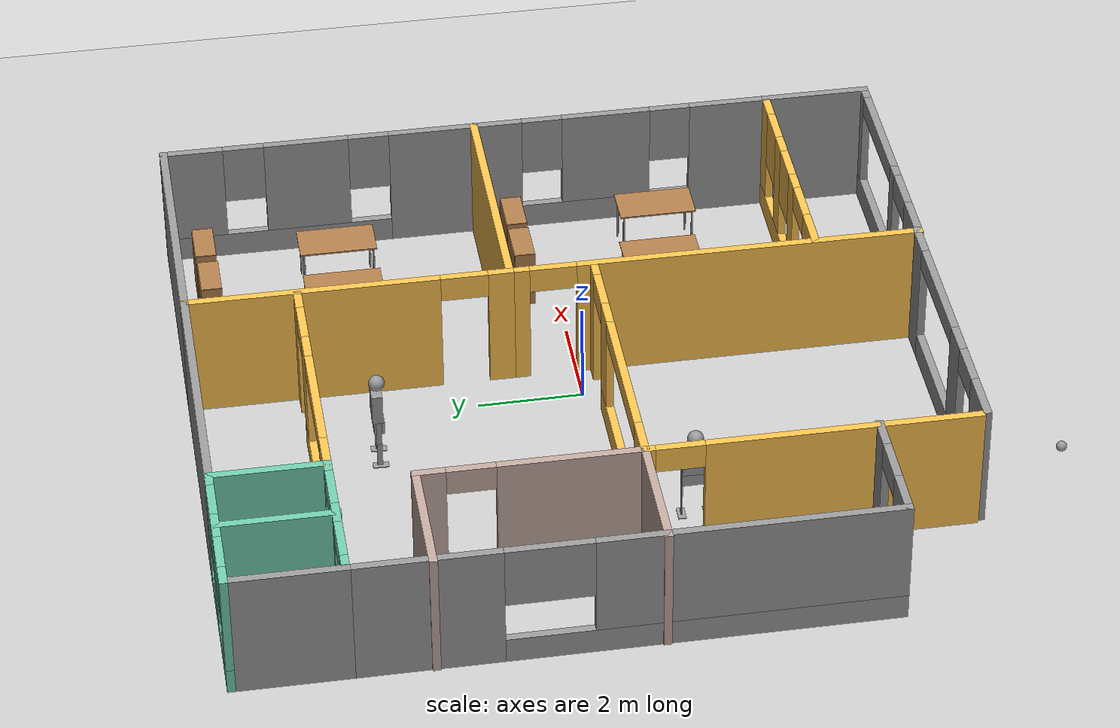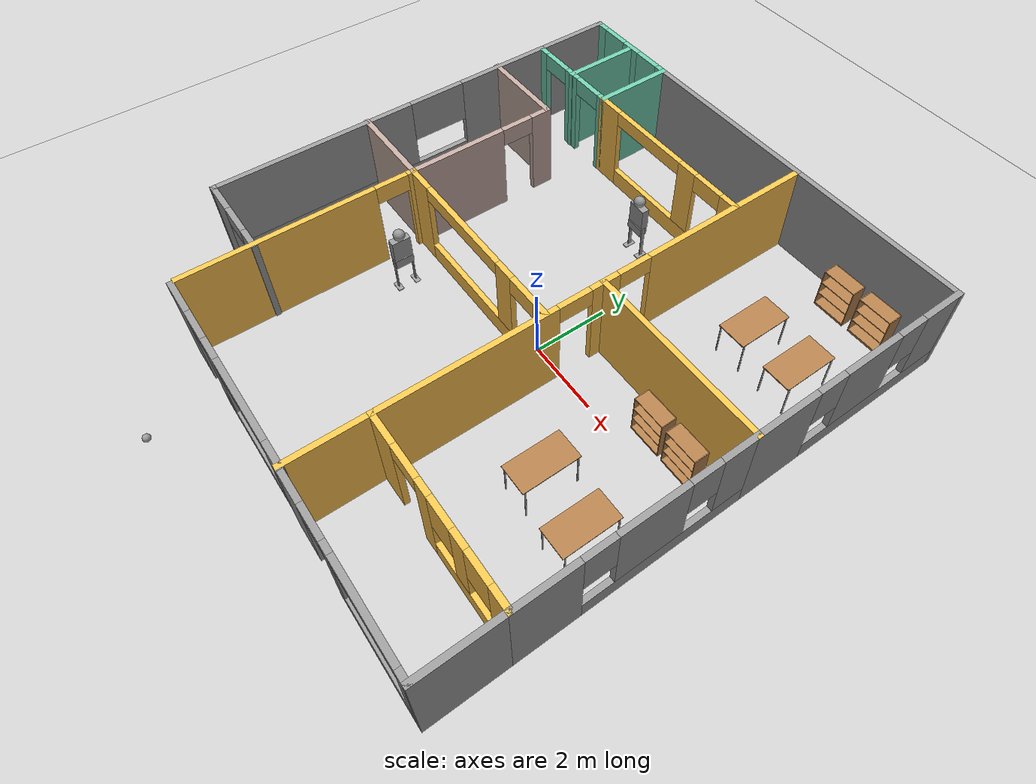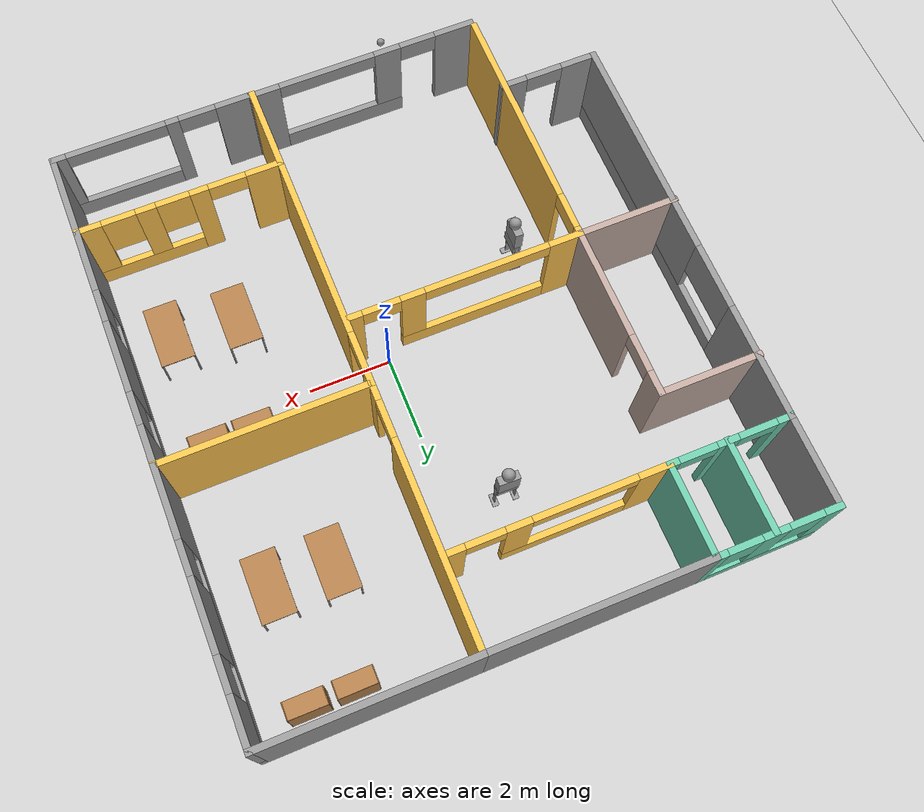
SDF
<sdf version="1.6">
 <world name="default">
  <plugin name="hello" filename="libhello.so"/>
  <light name="sun" type="directional">
   <pose>0 0 10 0 -0 0</pose>
   <diffuse>0.8 0.8 0.8 1</diffuse>
   <specular>0.2 0.2 0.2 1</specular>
   <attenuation>
    <range>1000</range>
    <constant>0.9</constant>
    <linear>0.01</linear>
    <quadratic>0.001</quadratic>
   </attenuation>
   <direction>-0.5 0.1 -0.9</direction>
  </light>
  <model name="ground_plane">
   <static>1</static>
   <link name="link">
    <collision name="collision">
     <geometry><plane><normal>0 0 1</normal><size>100 100</size></plane></geometry>
     <surface>
      <contact><collide_bitmask>65535</collide_bitmask></contact>
      <friction><ode><mu>100</mu><mu2>50</mu2></ode></friction>
     </surface>
    </collision>
    <visual name="visual">
     <cast_shadows>0</cast_shadows>
     <geometry><plane><normal>0 0 1</normal><size>100 100</size></plane></geometry>
     <material>
      <script><uri>file://media/materials/scripts/gazebo.material</uri><name>Gazebo/Grey</name></script>
     </material>
    </visual>
   </link>
  </model>
  <gravity>0 0 -9.8</gravity>
  <magnetic_field>6e-06 2.3e-05 -4.2e-05</magnetic_field>
  <atmosphere type="adiabatic"/>
  <physics name="default_physics" default="0" type="ode">
   <max_step_size>0.001</max_step_size>
   <real_time_factor>1</real_time_factor>
   <real_time_update_rate>1000</real_time_update_rate>
  </physics>
  <scene><ambient>0.4 0.4 0.4 1</ambient><background>0.7 0.7 0.7 1</background><shadows>1</shadows></scene>
  <audio><device>default</device></audio>
  <spherical_coordinates>
   <surface_model>EARTH_WGS84</surface_model>
   <latitude_deg>0</latitude_deg>
   <longitude_deg>0</longitude_deg>
   <elevation>0</elevation>
   <heading_deg>0</heading_deg>
  </spherical_coordinates>
  <model name="Building">
   <pose>-0.7405 0.37527 0 0 -0 0</pose>
   <link name="Wall_0">
    <pose>6.41568 -2.05 0 0 -0 1.5708</pose>
    <visual name="Wall_0_Visual_0">
     <pose>-2.18903 0 1.25 0 -0 0</pose>
     <geometry><box><size>1.62194 0.15 2.5</size></box></geometry>
     <material>
      <script><uri>file://media/materials/scripts/gazebo.material</uri><name>Gazebo/Grey</name></script>
      <ambient>1 1 1 1</ambient>
     </material>
     <meta><layer>0</layer></meta>
    </visual>
    <collision name="Wall_0_Collision_0">
     <geometry><box><size>1.62194 0.15 2.5</size></box></geometry>
     <pose>-2.18903 0 1.25 0 -0 0</pose>
    </collision>
    <visual name="Wall_0_Visual_1">
     <pose>0.81097 0 0.25 0 -0 0</pose>
     <geometry><box><size>4.37806 0.15 0.5</size></box></geometry>
     <material>
      <script><uri>file://media/materials/scripts/gazebo.material</uri><name>Gazebo/Grey</name></script>
      <ambient>1 1 1 1</ambient>
     </material>
     <meta><layer>0</layer></meta>
    </visual>
    <collision name="Wall_0_Collision_1">
     <geometry><box><size>4.37806 0.15 0.5</size></box></geometry>
     <pose>0.81097 0 0.25 0 -0 0</pose>
    </collision>
    <visual name="Wall_0_Visual_2">
     <pose>0.301348 0 1.5 0 -0 0</pose>
     <geometry><box><size>1.75882 0.15 2</size></box></geometry>
     <material>
      <script><uri>file://media/materials/scripts/gazebo.material</uri><name>Gazebo/Grey</name></script>
      <ambient>1 1 1 1</ambient>
     </material>
     <meta><layer>0</layer></meta>
    </visual>
    <collision name="Wall_0_Collision_2">
     <geometry><box><size>1.75882 0.15 2</size></box></geometry>
     <pose>0.301348 0 1.5 0 -0 0</pose>
    </collision>
    <visual name="Wall_0_Visual_3">
     <pose>2.49038 0 1.5 0 -0 0</pose>
     <geometry><box><size>1.01924 0.15 2</size></box></geometry>
     <material>
      <script><uri>file://media/materials/scripts/gazebo.material</uri><name>Gazebo/Grey</name></script>
      <ambient>1 1 1 1</ambient>
     </material>
     <meta><layer>0</layer></meta>
    </visual>
    <collision name="Wall_0_Collision_3">
     <geometry><box><size>1.01924 0.15 2</size></box></geometry>
     <pose>2.49038 0 1.5 0 -0 0</pose>
    </collision>
    <visual name="Wall_0_Visual_4">
     <pose>-0.97806 0 1.9 0 -0 0</pose>
     <geometry><box><size>0.8 0.15 1.2</size></box></geometry>
     <material>
      <script><uri>file://media/materials/scripts/gazebo.material</uri><name>Gazebo/Grey</name></script>
      <ambient>1 1 1 1</ambient>
     </material>
     <meta><layer>0</layer></meta>
    </visual>
    <collision name="Wall_0_Collision_4">
     <geometry><box><size>0.8 0.15 1.2</size></box></geometry>
     <pose>-0.97806 0 1.9 0 -0 0</pose>
    </collision>
    <visual name="Wall_0_Visual_5">
     <pose>1.58076 0 1.9 0 -0 0</pose>
     <geometry><box><size>0.8 0.15 1.2</size></box></geometry>
     <material>
      <script><uri>file://media/materials/scripts/gazebo.material</uri><name>Gazebo/Grey</name></script>
      <ambient>1 1 1 1</ambient>
     </material>
     <meta><layer>0</layer></meta>
    </visual>
    <collision name="Wall_0_Collision_5">
     <geometry><box><size>0.8 0.15 1.2</size></box></geometry>
     <pose>1.58076 0 1.9 0 -0 0</pose>
    </collision>
   </link>
   <link name="Wall_1">
    <collision name="Wall_1_Collision">
     <geometry><box><size>5 0.15 2.5</size></box></geometry>
     <pose>0 0 1.25 0 -0 0</pose>
    </collision>
    <visual name="Wall_1_Visual">
     <pose>0 0 1.25 0 -0 0</pose>
     <geometry><box><size>5 0.15 2.5</size></box></geometry>
     <material>
      <script><uri>file://media/materials/scripts/gazebo.material</uri><name>Gazebo/Grey</name></script>
      <ambient>1 0.764706 0.305882 1</ambient>
     </material>
     <meta><layer>0</layer></meta>
    </visual>
    <pose>3.99068 0.875 0 0 -0 3.14159</pose>
   </link>
   <link name="Wall_12">
    <collision name="Wall_12_Collision">
     <geometry><box><size>5.25 0.15 2.5</size></box></geometry>
     <pose>0 0 1.25 0 -0 0</pose>
    </collision>
    <visual name="Wall_12_Visual">
     <pose>0 0 1.25 0 -0 0</pose>
     <geometry><box><size>5.25 0.15 2.5</size></box></geometry>
     <material>
      <script><uri>file://media/materials/scripts/gazebo.material</uri><name>Gazebo/Grey</name></script>
      <ambient>1 1 1 1</ambient>
     </material>
     <meta><layer>0</layer></meta>
    </visual>
    <pose>-0.984323 6.975 0 0 -0 3.14159</pose>
   </link>
   <link name="Wall_13">
    <collision name="Wall_13_Collision">
     <geometry><box><size>2.25 0.15 2.5</size></box></geometry>
     <pose>0 0 1.25 0 -0 0</pose>
    </collision>
    <visual name="Wall_13_Visual">
     <pose>0 0 1.25 0 -0 0</pose>
     <geometry><box><size>2.25 0.15 2.5</size></box></geometry>
     <material>
      <script><uri>file://media/materials/scripts/gazebo.material</uri><name>Gazebo/Grey</name></script>
      <ambient>0.435294 0.796078 0.67451 1</ambient>
     </material>
     <meta><layer>0</layer></meta>
    </visual>
    <pose>-3.53432 5.925 0 0 -0 -1.5708</pose>
   </link>
   <link name="Wall_14">
    <pose>-0.984323 4.875 0 0 -0 0</pose>
    <visual name="Wall_14_Visual_0">
     <pose>-2.22764 0 1.25 0 -0 0</pose>
     <geometry><box><size>0.794723 0.15 2.5</size></box></geometry>
     <material>
      <script><uri>file://media/materials/scripts/gazebo.material</uri><name>Gazebo/Grey</name></script>
      <ambient>1 0.764706 0.305882 1</ambient>
     </material>
     <meta><layer>0</layer></meta>
    </visual>
    <collision name="Wall_14_Collision_0">
     <geometry><box><size>0.794723 0.15 2.5</size></box></geometry>
     <pose>-2.22764 0 1.25 0 -0 0</pose>
    </collision>
    <visual name="Wall_14_Visual_1">
     <pose>2.34319 0 1.25 0 -0 0</pose>
     <geometry><box><size>0.563624 0.15 2.5</size></box></geometry>
     <material>
      <script><uri>file://media/materials/scripts/gazebo.material</uri><name>Gazebo/Grey</name></script>
      <ambient>1 0.764706 0.305882 1</ambient>
     </material>
     <meta><layer>0</layer></meta>
    </visual>
    <collision name="Wall_14_Collision_1">
     <geometry><box><size>0.563624 0.15 2.5</size></box></geometry>
     <pose>2.34319 0 1.25 0 -0 0</pose>
    </collision>
    <visual name="Wall_14_Visual_2">
     <pose>-0.334451 0 0.25 0 -0 0</pose>
     <geometry><box><size>2.99165 0.15 0.5</size></box></geometry>
     <material>
      <script><uri>file://media/materials/scripts/gazebo.material</uri><name>Gazebo/Grey</name></script>
      <ambient>1 0.764706 0.305882 1</ambient>
     </material>
     <meta><layer>0</layer></meta>
    </visual>
    <collision name="Wall_14_Collision_2">
     <geometry><box><size>2.99165 0.15 0.5</size></box></geometry>
     <pose>-0.334451 0 0.25 0 -0 0</pose>
    </collision>
    <visual name="Wall_14_Visual_3">
     <pose>0.865549 0 1.5 0 -0 0</pose>
     <geometry><box><size>0.591654 0.15 2</size></box></geometry>
     <material>
      <script><uri>file://media/materials/scripts/gazebo.material</uri><name>Gazebo/Grey</name></script>
      <ambient>1 0.764706 0.305882 1</ambient>
     </material>
     <meta><layer>0</layer></meta>
    </visual>
    <collision name="Wall_14_Collision_3">
     <geometry><box><size>0.591654 0.15 2</size></box></geometry>
     <pose>0.865549 0 1.5 0 -0 0</pose>
    </collision>
    <visual name="Wall_14_Visual_4">
     <pose>1.61138 0 2.25 0 -0 0</pose>
     <geometry><box><size>0.9 0.15 0.5</size></box></geometry>
     <material>
      <script><uri>file://media/materials/scripts/gazebo.material</uri><name>Gazebo/Grey</name></script>
      <ambient>1 0.764706 0.305882 1</ambient>
     </material>
     <meta><layer>0</layer></meta>
    </visual>
    <collision name="Wall_14_Collision_4">
     <geometry><box><size>0.9 0.15 0.5</size></box></geometry>
     <pose>1.61138 0 2.25 0 -0 0</pose>
    </collision>
    <visual name="Wall_14_Visual_5">
     <pose>-0.630277 0 2.3 0 -0 0</pose>
     <geometry><box><size>2.4 0.15 0.4</size></box></geometry>
     <material>
      <script><uri>file://media/materials/scripts/gazebo.material</uri><name>Gazebo/Grey</name></script>
      <ambient>1 0.764706 0.305882 1</ambient>
     </material>
     <meta><layer>0</layer></meta>
    </visual>
    <collision name="Wall_14_Collision_5">
     <geometry><box><size>2.4 0.15 0.4</size></box></geometry>
     <pose>-0.630277 0 2.3 0 -0 0</pose>
    </collision>
   </link>
   <link name="Wall_16">
    <pose>-4.95932 6.975 0 0 -0 3.14159</pose>
    <visual name="Wall_16_Visual_0">
     <pose>-1.33173 0 1.25 0 -0 0</pose>
     <geometry><box><size>0.336546 0.15 2.5</size></box></geometry>
     <material>
      <script><uri>file://media/materials/scripts/gazebo.material</uri><name>Gazebo/Grey</name></script>
      <ambient>0.435294 0.796078 0.67451 1</ambient>
     </material>
     <meta><layer>0</layer></meta>
    </visual>
    <collision name="Wall_16_Collision_0">
     <geometry><box><size>0.336546 0.15 2.5</size></box></geometry>
     <pose>-1.33173 0 1.25 0 -0 0</pose>
    </collision>
    <visual name="Wall_16_Visual_1">
     <pose>0.168273 0 0.25 0 -0 0</pose>
     <geometry><box><size>2.66345 0.15 0.5</size></box></geometry>
     <material>
      <script><uri>file://media/materials/scripts/gazebo.material</uri><name>Gazebo/Grey</name></script>
      <ambient>0.435294 0.796078 0.67451 1</ambient>
     </material>
     <meta><layer>0</layer></meta>
    </visual>
    <collision name="Wall_16_Collision_1">
     <geometry><box><size>2.66345 0.15 0.5</size></box></geometry>
     <pose>0.168273 0 0.25 0 -0 0</pose>
    </collision>
    <visual name="Wall_16_Visual_2">
     <pose>-0.053965 0 1.5 0 -0 0</pose>
     <geometry><box><size>0.618979 0.15 2</size></box></geometry>
     <material>
      <script><uri>file://media/materials/scripts/gazebo.material</uri><name>Gazebo/Grey</name></script>
      <ambient>0.435294 0.796078 0.67451 1</ambient>
     </material>
     <meta><layer>0</layer></meta>
    </visual>
    <collision name="Wall_16_Collision_2">
     <geometry><box><size>0.618979 0.15 2</size></box></geometry>
     <pose>-0.053965 0 1.5 0 -0 0</pose>
    </collision>
    <visual name="Wall_16_Visual_3">
     <pose>1.27776 0 1.5 0 -0 0</pose>
     <geometry><box><size>0.444475 0.15 2</size></box></geometry>
     <material>
      <script><uri>file://media/materials/scripts/gazebo.material</uri><name>Gazebo/Grey</name></script>
      <ambient>0.435294 0.796078 0.67451 1</ambient>
     </material>
     <meta><layer>0</layer></meta>
    </visual>
    <collision name="Wall_16_Collision_3">
     <geometry><box><size>0.444475 0.15 2</size></box></geometry>
     <pose>1.27776 0 1.5 0 -0 0</pose>
    </collision>
    <visual name="Wall_16_Visual_4">
     <pose>-0.763454 0 1.9 0 -0 0</pose>
     <geometry><box><size>0.8 0.15 1.2</size></box></geometry>
     <material>
      <script><uri>file://media/materials/scripts/gazebo.material</uri><name>Gazebo/Grey</name></script>
      <ambient>0.435294 0.796078 0.67451 1</ambient>
     </material>
     <meta><layer>0</layer></meta>
    </visual>
    <collision name="Wall_16_Collision_4">
     <geometry><box><size>0.8 0.15 1.2</size></box></geometry>
     <pose>-0.763454 0 1.9 0 -0 0</pose>
    </collision>
    <visual name="Wall_16_Visual_5">
     <pose>0.655525 0 1.9 0 -0 0</pose>
     <geometry><box><size>0.8 0.15 1.2</size></box></geometry>
     <material>
      <script><uri>file://media/materials/scripts/gazebo.material</uri><name>Gazebo/Grey</name></script>
      <ambient>0.435294 0.796078 0.67451 1</ambient>
     </material>
     <meta><layer>0</layer></meta>
    </visual>
    <collision name="Wall_16_Collision_5">
     <geometry><box><size>0.8 0.15 1.2</size></box></geometry>
     <pose>0.655525 0 1.9 0 -0 0</pose>
    </collision>
   </link>
   <link name="Wall_24">
    <collision name="Wall_24_Collision">
     <geometry><box><size>2.25 0.15 2.5</size></box></geometry>
     <pose>0 0 1.25 0 -0 0</pose>
    </collision>
    <visual name="Wall_24_Visual">
     <pose>0 0 1.25 0 -0 0</pose>
     <geometry><box><size>2.25 0.15 2.5</size></box></geometry>
     <material>
      <script><uri>file://media/materials/scripts/gazebo.material</uri><name>Gazebo/Grey</name></script>
      <ambient>1 1 1 1</ambient>
     </material>
     <meta><layer>0</layer></meta>
    </visual>
    <pose>-6.38432 5.925 0 0 -0 -1.5708</pose>
   </link>
   <link name="Wall_25">
    <pose>-4.95932 4.875 0 0 -0 0</pose>
    <visual name="Wall_25_Visual_0">
     <pose>-1.29513 0 1.25 0 -0 0</pose>
     <geometry><box><size>0.409735 0.15 2.5</size></box></geometry>
     <material>
      <script><uri>file://media/materials/scripts/gazebo.material</uri><name>Gazebo/Grey</name></script>
      <ambient>0.435294 0.796078 0.67451 1</ambient>
     </material>
     <meta><layer>0</layer></meta>
    </visual>
    <collision name="Wall_25_Collision_0">
     <geometry><box><size>0.409735 0.15 2.5</size></box></geometry>
     <pose>-1.29513 0 1.25 0 -0 0</pose>
    </collision>
    <visual name="Wall_25_Visual_1">
     <pose>0.063311 0 1.25 0 -0 0</pose>
     <geometry><box><size>0.50715 0.15 2.5</size></box></geometry>
     <material>
      <script><uri>file://media/materials/scripts/gazebo.material</uri><name>Gazebo/Grey</name></script>
      <ambient>0.435294 0.796078 0.67451 1</ambient>
     </material>
     <meta><layer>0</layer></meta>
    </visual>
    <collision name="Wall_25_Collision_1">
     <geometry><box><size>0.50715 0.15 2.5</size></box></geometry>
     <pose>0.063311 0 1.25 0 -0 0</pose>
    </collision>
    <visual name="Wall_25_Visual_2">
     <pose>1.35844 0 1.25 0 -0 0</pose>
     <geometry><box><size>0.283114 0.15 2.5</size></box></geometry>
     <material>
      <script><uri>file://media/materials/scripts/gazebo.material</uri><name>Gazebo/Grey</name></script>
      <ambient>0.435294 0.796078 0.67451 1</ambient>
     </material>
     <meta><layer>0</layer></meta>
    </visual>
    <collision name="Wall_25_Collision_2">
     <geometry><box><size>0.283114 0.15 2.5</size></box></geometry>
     <pose>1.35844 0 1.25 0 -0 0</pose>
    </collision>
    <visual name="Wall_25_Visual_3">
     <pose>-0.640265 0 2.25 0 -0 0</pose>
     <geometry><box><size>0.9 0.15 0.5</size></box></geometry>
     <material>
      <script><uri>file://media/materials/scripts/gazebo.material</uri><name>Gazebo/Grey</name></script>
      <ambient>0.435294 0.796078 0.67451 1</ambient>
     </material>
     <meta><layer>0</layer></meta>
    </visual>
    <collision name="Wall_25_Collision_3">
     <geometry><box><size>0.9 0.15 0.5</size></box></geometry>
     <pose>-0.640265 0 2.25 0 -0 0</pose>
    </collision>
    <visual name="Wall_25_Visual_4">
     <pose>0.766886 0 2.25 0 -0 0</pose>
     <geometry><box><size>0.9 0.15 0.5</size></box></geometry>
     <material>
      <script><uri>file://media/materials/scripts/gazebo.material</uri><name>Gazebo/Grey</name></script>
      <ambient>0.435294 0.796078 0.67451 1</ambient>
     </material>
     <meta><layer>0</layer></meta>
    </visual>
    <collision name="Wall_25_Collision_4">
     <geometry><box><size>0.9 0.15 0.5</size></box></geometry>
     <pose>0.766886 0 2.25 0 -0 0</pose>
    </collision>
   </link>
   <link name="Wall_27">
    <pose>-6.38432 -0.05 0 0 -0 -1.5708</pose>
    <visual name="Wall_27_Visual_0">
     <pose>-3.60177 0 1.25 0 -0 0</pose>
     <geometry><box><size>2.79646 0.15 2.5</size></box></geometry>
     <material>
      <script><uri>file://media/materials/scripts/gazebo.material</uri><name>Gazebo/Grey</name></script>
      <ambient>1 1 1 1</ambient>
     </material>
     <meta><layer>0</layer></meta>
    </visual>
    <collision name="Wall_27_Collision_0">
     <geometry><box><size>2.79646 0.15 2.5</size></box></geometry>
     <pose>-3.60177 0 1.25 0 -0 0</pose>
    </collision>
    <visual name="Wall_27_Visual_1">
     <pose>1.39823 0 0.25 0 -0 0</pose>
     <geometry><box><size>7.20354 0.15 0.5</size></box></geometry>
     <material>
      <script><uri>file://media/materials/scripts/gazebo.material</uri><name>Gazebo/Grey</name></script>
      <ambient>1 1 1 1</ambient>
     </material>
     <meta><layer>0</layer></meta>
    </visual>
    <collision name="Wall_27_Collision_1">
     <geometry><box><size>7.20354 0.15 0.5</size></box></geometry>
     <pose>1.39823 0 0.25 0 -0 0</pose>
    </collision>
    <visual name="Wall_27_Visual_2">
     <pose>2.19823 0 1.5 0 -0 0</pose>
     <geometry><box><size>5.60354 0.15 2</size></box></geometry>
     <material>
      <script><uri>file://media/materials/scripts/gazebo.material</uri><name>Gazebo/Grey</name></script>
      <ambient>1 1 1 1</ambient>
     </material>
     <meta><layer>0</layer></meta>
    </visual>
    <collision name="Wall_27_Collision_2">
     <geometry><box><size>5.60354 0.15 2</size></box></geometry>
     <pose>2.19823 0 1.5 0 -0 0</pose>
    </collision>
    <visual name="Wall_27_Visual_3">
     <pose>-1.40354 0 1.9 0 -0 0</pose>
     <geometry><box><size>1.6 0.15 1.2</size></box></geometry>
     <material>
      <script><uri>file://media/materials/scripts/gazebo.material</uri><name>Gazebo/Grey</name></script>
      <ambient>1 1 1 1</ambient>
     </material>
     <meta><layer>0</layer></meta>
    </visual>
    <collision name="Wall_27_Collision_3">
     <geometry><box><size>1.6 0.15 1.2</size></box></geometry>
     <pose>-1.40354 0 1.9 0 -0 0</pose>
    </collision>
   </link>
   <link name="Wall_3">
    <pose>3.99068 -4.975 0 0 -0 0</pose>
    <visual name="Wall_3_Visual_0">
     <pose>-2.03846 0 1.25 0 -0 0</pose>
     <geometry><box><size>0.923088 0.15 2.5</size></box></geometry>
     <material>
      <script><uri>file://media/materials/scripts/gazebo.material</uri><name>Gazebo/Grey</name></script>
      <ambient>1 0.764706 0.305882 1</ambient>
     </material>
     <meta><layer>0</layer></meta>
    </visual>
    <collision name="Wall_3_Collision_0">
     <geometry><box><size>0.923088 0.15 2.5</size></box></geometry>
     <pose>-2.03846 0 1.25 0 -0 0</pose>
    </collision>
    <visual name="Wall_3_Visual_1">
     <pose>-0.452103 0 1.25 0 -0 0</pose>
     <geometry><box><size>0.449617 0.15 2.5</size></box></geometry>
     <material>
      <script><uri>file://media/materials/scripts/gazebo.material</uri><name>Gazebo/Grey</name></script>
      <ambient>1 0.764706 0.305882 1</ambient>
     </material>
     <meta><layer>0</layer></meta>
    </visual>
    <collision name="Wall_3_Collision_1">
     <geometry><box><size>0.449617 0.15 2.5</size></box></geometry>
     <pose>-0.452103 0 1.25 0 -0 0</pose>
    </collision>
    <visual name="Wall_3_Visual_2">
     <pose>1.13635 0 0.25 0 -0 0</pose>
     <geometry><box><size>2.72729 0.15 0.5</size></box></geometry>
     <material>
      <script><uri>file://media/materials/scripts/gazebo.material</uri><name>Gazebo/Grey</name></script>
      <ambient>1 0.764706 0.305882 1</ambient>
     </material>
     <meta><layer>0</layer></meta>
    </visual>
    <collision name="Wall_3_Collision_2">
     <geometry><box><size>2.72729 0.15 0.5</size></box></geometry>
     <pose>1.13635 0 0.25 0 -0 0</pose>
    </collision>
    <visual name="Wall_3_Visual_3">
     <pose>0.812409 0 1.5 0 -0 0</pose>
     <geometry><box><size>0.479408 0.15 2</size></box></geometry>
     <material>
      <script><uri>file://media/materials/scripts/gazebo.material</uri><name>Gazebo/Grey</name></script>
      <ambient>1 0.764706 0.305882 1</ambient>
     </material>
     <meta><layer>0</layer></meta>
    </visual>
    <collision name="Wall_3_Collision_3">
     <geometry><box><size>0.479408 0.15 2</size></box></geometry>
     <pose>0.812409 0 1.5 0 -0 0</pose>
    </collision>
    <visual name="Wall_3_Visual_4">
     <pose>2.17606 0 1.5 0 -0 0</pose>
     <geometry><box><size>0.647887 0.15 2</size></box></geometry>
     <material>
      <script><uri>file://media/materials/scripts/gazebo.material</uri><name>Gazebo/Grey</name></script>
      <ambient>1 0.764706 0.305882 1</ambient>
     </material>
     <meta><layer>0</layer></meta>
    </visual>
    <collision name="Wall_3_Collision_4">
     <geometry><box><size>0.647887 0.15 2</size></box></geometry>
     <pose>2.17606 0 1.5 0 -0 0</pose>
    </collision>
    <visual name="Wall_3_Visual_5">
     <pose>0.172705 0 1.9 0 -0 0</pose>
     <geometry><box><size>0.8 0.15 1.2</size></box></geometry>
     <material>
      <script><uri>file://media/materials/scripts/gazebo.material</uri><name>Gazebo/Grey</name></script>
      <ambient>1 0.764706 0.305882 1</ambient>
     </material>
     <meta><layer>0</layer></meta>
    </visual>
    <collision name="Wall_3_Collision_5">
     <geometry><box><size>0.8 0.15 1.2</size></box></geometry>
     <pose>0.172705 0 1.9 0 -0 0</pose>
    </collision>
    <visual name="Wall_3_Visual_6">
     <pose>1.45211 0 1.9 0 -0 0</pose>
     <geometry><box><size>0.8 0.15 1.2</size></box></geometry>
     <material>
      <script><uri>file://media/materials/scripts/gazebo.material</uri><name>Gazebo/Grey</name></script>
      <ambient>1 0.764706 0.305882 1</ambient>
     </material>
     <meta><layer>0</layer></meta>
    </visual>
    <collision name="Wall_3_Collision_6">
     <geometry><box><size>0.8 0.15 1.2</size></box></geometry>
     <pose>1.45211 0 1.9 0 -0 0</pose>
    </collision>
    <visual name="Wall_3_Visual_7">
     <pose>-1.12691 0 2.25 0 -0 0</pose>
     <geometry><box><size>0.9 0.15 0.5</size></box></geometry>
     <material>
      <script><uri>file://media/materials/scripts/gazebo.material</uri><name>Gazebo/Grey</name></script>
      <ambient>1 0.764706 0.305882 1</ambient>
     </material>
     <meta><layer>0</layer></meta>
    </visual>
    <collision name="Wall_3_Collision_7">
     <geometry><box><size>0.9 0.15 0.5</size></box></geometry>
     <pose>-1.12691 0 2.25 0 -0 0</pose>
    </collision>
   </link>
   <link name="Wall_30">
    <collision name="Wall_30_Collision">
     <geometry><box><size>2.5 0.15 2.5</size></box></geometry>
     <pose>0 0 1.25 0 -0 0</pose>
    </collision>
    <visual name="Wall_30_Visual">
     <pose>0 0 1.25 0 -0 0</pose>
     <geometry><box><size>2.5 0.15 2.5</size></box></geometry>
     <material>
      <script><uri>file://media/materials/scripts/gazebo.material</uri><name>Gazebo/Grey</name></script>
      <ambient>0.760784 0.662745 0.627451 1</ambient>
     </material>
     <meta><layer>0</layer></meta>
    </visual>
    <pose>-5.24068 3.38074 0 0 -0 0</pose>
   </link>
   <link name="Wall_31">
    <pose>-4.06568 1.33074 0 0 -0 -1.5708</pose>
    <visual name="Wall_31_Visual_0">
     <pose>-1.82051 0 1.25 0 -0 0</pose>
     <geometry><box><size>0.608974 0.15 2.5</size></box></geometry>
     <material>
      <script><uri>file://media/materials/scripts/gazebo.material</uri><name>Gazebo/Grey</name></script>
      <ambient>0.760784 0.662745 0.627451 1</ambient>
     </material>
     <meta><layer>0</layer></meta>
    </visual>
    <collision name="Wall_31_Collision_0">
     <geometry><box><size>0.608974 0.15 2.5</size></box></geometry>
     <pose>-1.82051 0 1.25 0 -0 0</pose>
    </collision>
    <visual name="Wall_31_Visual_1">
     <pose>0.754487 0 1.25 0 -0 0</pose>
     <geometry><box><size>2.74103 0.15 2.5</size></box></geometry>
     <material>
      <script><uri>file://media/materials/scripts/gazebo.material</uri><name>Gazebo/Grey</name></script>
      <ambient>0.760784 0.662745 0.627451 1</ambient>
     </material>
     <meta><layer>0</layer></meta>
    </visual>
    <collision name="Wall_31_Collision_1">
     <geometry><box><size>2.74103 0.15 2.5</size></box></geometry>
     <pose>0.754487 0 1.25 0 -0 0</pose>
    </collision>
    <visual name="Wall_31_Visual_2">
     <pose>-1.06603 0 2.25 0 -0 0</pose>
     <geometry><box><size>0.9 0.15 0.5</size></box></geometry>
     <material>
      <script><uri>file://media/materials/scripts/gazebo.material</uri><name>Gazebo/Grey</name></script>
      <ambient>0.760784 0.662745 0.627451 1</ambient>
     </material>
     <meta><layer>0</layer></meta>
    </visual>
    <collision name="Wall_31_Collision_2">
     <geometry><box><size>0.9 0.15 0.5</size></box></geometry>
     <pose>-1.06603 0 2.25 0 -0 0</pose>
    </collision>
   </link>
   <link name="Wall_34">
    <pose>-1.26568 -0.719262 0 0 -0 0</pose>
    <visual name="Wall_34_Visual_0">
     <pose>-2.45687 0 1.25 0 -0 0</pose>
     <geometry><box><size>0.836268 0.15 2.5</size></box></geometry>
     <material>
      <script><uri>file://media/materials/scripts/gazebo.material</uri><name>Gazebo/Grey</name></script>
      <ambient>1 0.764706 0.305882 1</ambient>
     </material>
     <meta><layer>0</layer></meta>
    </visual>
    <collision name="Wall_34_Collision_0">
     <geometry><box><size>0.836268 0.15 2.5</size></box></geometry>
     <pose>-2.45687 0 1.25 0 -0 0</pose>
    </collision>
    <visual name="Wall_34_Visual_1">
     <pose>2.65737 0 1.25 0 -0 0</pose>
     <geometry><box><size>0.435259 0.15 2.5</size></box></geometry>
     <material>
      <script><uri>file://media/materials/scripts/gazebo.material</uri><name>Gazebo/Grey</name></script>
      <ambient>1 0.764706 0.305882 1</ambient>
     </material>
     <meta><layer>0</layer></meta>
    </visual>
    <collision name="Wall_34_Collision_1">
     <geometry><box><size>0.435259 0.15 2.5</size></box></geometry>
     <pose>2.65737 0 1.25 0 -0 0</pose>
    </collision>
    <visual name="Wall_34_Visual_2">
     <pose>-0.249495 0 0.25 0 -0 0</pose>
     <geometry><box><size>3.57847 0.15 0.5</size></box></geometry>
     <material>
      <script><uri>file://media/materials/scripts/gazebo.material</uri><name>Gazebo/Grey</name></script>
      <ambient>1 0.764706 0.305882 1</ambient>
     </material>
     <meta><layer>0</layer></meta>
    </visual>
    <collision name="Wall_34_Collision_2">
     <geometry><box><size>3.57847 0.15 0.5</size></box></geometry>
     <pose>-0.249495 0 0.25 0 -0 0</pose>
    </collision>
    <visual name="Wall_34_Visual_3">
     <pose>1.2505 0 1.5 0 -0 0</pose>
     <geometry><box><size>0.578474 0.15 2</size></box></geometry>
     <material>
      <script><uri>file://media/materials/scripts/gazebo.material</uri><name>Gazebo/Grey</name></script>
      <ambient>1 0.764706 0.305882 1</ambient>
     </material>
     <meta><layer>0</layer></meta>
    </visual>
    <collision name="Wall_34_Collision_3">
     <geometry><box><size>0.578474 0.15 2</size></box></geometry>
     <pose>1.2505 0 1.5 0 -0 0</pose>
    </collision>
    <visual name="Wall_34_Visual_4">
     <pose>1.98974 0 2.25 0 -0 0</pose>
     <geometry><box><size>0.9 0.15 0.5</size></box></geometry>
     <material>
      <script><uri>file://media/materials/scripts/gazebo.material</uri><name>Gazebo/Grey</name></script>
      <ambient>1 0.764706 0.305882 1</ambient>
     </material>
     <meta><layer>0</layer></meta>
    </visual>
    <collision name="Wall_34_Collision_4">
     <geometry><box><size>0.9 0.15 0.5</size></box></geometry>
     <pose>1.98974 0 2.25 0 -0 0</pose>
    </collision>
    <visual name="Wall_34_Visual_5">
     <pose>-0.538732 0 2.3 0 -0 0</pose>
     <geometry><box><size>3 0.15 0.4</size></box></geometry>
     <material>
      <script><uri>file://media/materials/scripts/gazebo.material</uri><name>Gazebo/Grey</name></script>
      <ambient>1 0.764706 0.305882 1</ambient>
     </material>
     <meta><layer>0</layer></meta>
    </visual>
    <collision name="Wall_34_Collision_5">
     <geometry><box><size>3 0.15 0.4</size></box></geometry>
     <pose>-0.538732 0 2.3 0 -0 0</pose>
    </collision>
   </link>
   <link name="Wall_36">
    <pose>-5.20932 -4.975 0 0 -0 0</pose>
    <visual name="Wall_36_Visual_0">
     <pose>-0.782538 0 1.25 0 -0 0</pose>
     <geometry><box><size>0.934924 0.15 2.5</size></box></geometry>
     <material>
      <script><uri>file://media/materials/scripts/gazebo.material</uri><name>Gazebo/Grey</name></script>
      <ambient>1 1 1 1</ambient>
     </material>
     <meta><layer>0</layer></meta>
    </visual>
    <collision name="Wall_36_Collision_0">
     <geometry><box><size>0.934924 0.15 2.5</size></box></geometry>
     <pose>-0.782538 0 1.25 0 -0 0</pose>
    </collision>
    <visual name="Wall_36_Visual_1">
     <pose>0.917462 0 1.25 0 -0 0</pose>
     <geometry><box><size>0.665076 0.15 2.5</size></box></geometry>
     <material>
      <script><uri>file://media/materials/scripts/gazebo.material</uri><name>Gazebo/Grey</name></script>
      <ambient>1 1 1 1</ambient>
     </material>
     <meta><layer>0</layer></meta>
    </visual>
    <collision name="Wall_36_Collision_1">
     <geometry><box><size>0.665076 0.15 2.5</size></box></geometry>
     <pose>0.917462 0 1.25 0 -0 0</pose>
    </collision>
    <visual name="Wall_36_Visual_2">
     <pose>0.134924 0 2.25 0 -0 0</pose>
     <geometry><box><size>0.9 0.15 0.5</size></box></geometry>
     <material>
      <script><uri>file://media/materials/scripts/gazebo.material</uri><name>Gazebo/Grey</name></script>
      <ambient>1 1 1 1</ambient>
     </material>
     <meta><layer>0</layer></meta>
    </visual>
    <collision name="Wall_36_Collision_2">
     <geometry><box><size>0.9 0.15 0.5</size></box></geometry>
     <pose>0.134924 0 2.25 0 -0 0</pose>
    </collision>
   </link>
   <link name="Wall_42">
    <collision name="Wall_42_Collision">
     <geometry><box><size>2.5 0.15 2.5</size></box></geometry>
     <pose>0 0 1.25 0 -0 0</pose>
    </collision>
    <visual name="Wall_42_Visual">
     <pose>0 0 1.25 0 -0 0</pose>
     <geometry><box><size>2.5 0.15 2.5</size></box></geometry>
     <material>
      <script><uri>file://media/materials/scripts/gazebo.material</uri><name>Gazebo/Grey</name></script>
      <ambient>0.760784 0.662745 0.627451 1</ambient>
     </material>
     <meta><layer>0</layer></meta>
    </visual>
    <pose>-5.24068 -0.719262 0 0 -0 3.14159</pose>
   </link>
   <link name="Wall_46">
    <pose>-1.20772 -6.9484 0 0 -0 3.14159</pose>
    <visual name="Wall_46_Visual_0">
     <pose>-2.49181 0 1.25 0 -0 0</pose>
     <geometry><box><size>0.766375 0.15 2.5</size></box></geometry>
     <material>
      <script><uri>file://media/materials/scripts/gazebo.material</uri><name>Gazebo/Grey</name></script>
      <ambient>1 1 1 1</ambient>
     </material>
     <meta><layer>0</layer></meta>
    </visual>
    <collision name="Wall_46_Collision_0">
     <geometry><box><size>0.766375 0.15 2.5</size></box></geometry>
     <pose>-2.49181 0 1.25 0 -0 0</pose>
    </collision>
    <visual name="Wall_46_Visual_1">
     <pose>2.36458 0 1.25 0 -0 0</pose>
     <geometry><box><size>1.02084 0.15 2.5</size></box></geometry>
     <material>
      <script><uri>file://media/materials/scripts/gazebo.material</uri><name>Gazebo/Grey</name></script>
      <ambient>1 1 1 1</ambient>
     </material>
     <meta><layer>0</layer></meta>
    </visual>
    <collision name="Wall_46_Collision_1">
     <geometry><box><size>1.02084 0.15 2.5</size></box></geometry>
     <pose>2.36458 0 1.25 0 -0 0</pose>
    </collision>
    <visual name="Wall_46_Visual_2">
     <pose>-0.577231 0 0.25 0 -0 0</pose>
     <geometry><box><size>3.06279 0.15 0.5</size></box></geometry>
     <material>
      <script><uri>file://media/materials/scripts/gazebo.material</uri><name>Gazebo/Grey</name></script>
      <ambient>1 1 1 1</ambient>
     </material>
     <meta><layer>0</layer></meta>
    </visual>
    <collision name="Wall_46_Collision_2">
     <geometry><box><size>3.06279 0.15 0.5</size></box></geometry>
     <pose>-0.577231 0 0.25 0 -0 0</pose>
    </collision>
    <visual name="Wall_46_Visual_3">
     <pose>0.622769 0 1.5 0 -0 0</pose>
     <geometry><box><size>0.662788 0.15 2</size></box></geometry>
     <material>
      <script><uri>file://media/materials/scripts/gazebo.material</uri><name>Gazebo/Grey</name></script>
      <ambient>1 1 1 1</ambient>
     </material>
     <meta><layer>0</layer></meta>
    </visual>
    <collision name="Wall_46_Collision_3">
     <geometry><box><size>0.662788 0.15 2</size></box></geometry>
     <pose>0.622769 0 1.5 0 -0 0</pose>
    </collision>
    <visual name="Wall_46_Visual_4">
     <pose>1.40416 0 2.25 0 -0 0</pose>
     <geometry><box><size>0.9 0.15 0.5</size></box></geometry>
     <material>
      <script><uri>file://media/materials/scripts/gazebo.material</uri><name>Gazebo/Grey</name></script>
      <ambient>1 1 1 1</ambient>
     </material>
     <meta><layer>0</layer></meta>
    </visual>
    <collision name="Wall_46_Collision_4">
     <geometry><box><size>0.9 0.15 0.5</size></box></geometry>
     <pose>1.40416 0 2.25 0 -0 0</pose>
    </collision>
    <visual name="Wall_46_Visual_5">
     <pose>-0.908625 0 2.3 0 -0 0</pose>
     <geometry><box><size>2.4 0.15 0.4</size></box></geometry>
     <material>
      <script><uri>file://media/materials/scripts/gazebo.material</uri><name>Gazebo/Grey</name></script>
      <ambient>1 1 1 1</ambient>
     </material>
     <meta><layer>0</layer></meta>
    </visual>
    <collision name="Wall_46_Collision_5">
     <geometry><box><size>2.4 0.15 0.4</size></box></geometry>
     <pose>-0.908625 0 2.3 0 -0 0</pose>
    </collision>
   </link>
   <link name="Wall_52">
    <pose>-4.06568 -3.76926 0 0 -0 -1.5708</pose>
    <visual name="Wall_52_Visual_0">
     <pose>-2.99686 0 1.25 0 -0 0</pose>
     <geometry><box><size>0.256277 0.15 2.5</size></box></geometry>
     <material>
      <script><uri>file://media/materials/scripts/gazebo.material</uri><name>Gazebo/Grey</name></script>
      <ambient>1 0.764706 0.305882 1</ambient>
     </material>
     <meta><layer>0</layer></meta>
    </visual>
    <collision name="Wall_52_Collision_0">
     <geometry><box><size>0.256277 0.15 2.5</size></box></geometry>
     <pose>-2.99686 0 1.25 0 -0 0</pose>
    </collision>
    <visual name="Wall_52_Visual_1">
     <pose>0.578139 0 1.25 0 -0 0</pose>
     <geometry><box><size>5.09372 0.15 2.5</size></box></geometry>
     <material>
      <script><uri>file://media/materials/scripts/gazebo.material</uri><name>Gazebo/Grey</name></script>
      <ambient>1 0.764706 0.305882 1</ambient>
     </material>
     <meta><layer>0</layer></meta>
    </visual>
    <collision name="Wall_52_Collision_1">
     <geometry><box><size>5.09372 0.15 2.5</size></box></geometry>
     <pose>0.578139 0 1.25 0 -0 0</pose>
    </collision>
    <visual name="Wall_52_Visual_2">
     <pose>-2.41872 0 2.25 0 -0 0</pose>
     <geometry><box><size>0.9 0.15 0.5</size></box></geometry>
     <material>
      <script><uri>file://media/materials/scripts/gazebo.material</uri><name>Gazebo/Grey</name></script>
      <ambient>1 0.764706 0.305882 1</ambient>
     </material>
     <meta><layer>0</layer></meta>
    </visual>
    <collision name="Wall_52_Collision_2">
     <geometry><box><size>0.9 0.15 0.5</size></box></geometry>
     <pose>-2.41872 0 2.25 0 -0 0</pose>
    </collision>
   </link>
   <link name="Wall_54">
    <pose>1.56568 -3.05 0 0 -0 -1.5708</pose>
    <visual name="Wall_54_Visual_0">
     <pose>-3.77831 0 1.25 0 -0 0</pose>
     <geometry><box><size>0.443388 0.15 2.5</size></box></geometry>
     <material>
      <script><uri>file://media/materials/scripts/gazebo.material</uri><name>Gazebo/Grey</name></script>
      <ambient>1 0.764706 0.305882 1</ambient>
     </material>
     <meta><layer>0</layer></meta>
    </visual>
    <collision name="Wall_54_Collision_0">
     <geometry><box><size>0.443388 0.15 2.5</size></box></geometry>
     <pose>-3.77831 0 1.25 0 -0 0</pose>
    </collision>
    <visual name="Wall_54_Visual_1">
     <pose>0.671694 0 1.25 0 -0 0</pose>
     <geometry><box><size>6.65661 0.15 2.5</size></box></geometry>
     <material>
      <script><uri>file://media/materials/scripts/gazebo.material</uri><name>Gazebo/Grey</name></script>
      <ambient>1 0.764706 0.305882 1</ambient>
     </material>
     <meta><layer>0</layer></meta>
    </visual>
    <collision name="Wall_54_Collision_1">
     <geometry><box><size>6.65661 0.15 2.5</size></box></geometry>
     <pose>0.671694 0 1.25 0 -0 0</pose>
    </collision>
    <visual name="Wall_54_Visual_2">
     <pose>-3.10661 0 2.25 0 -0 0</pose>
     <geometry><box><size>0.9 0.15 0.5</size></box></geometry>
     <material>
      <script><uri>file://media/materials/scripts/gazebo.material</uri><name>Gazebo/Grey</name></script>
      <ambient>1 0.764706 0.305882 1</ambient>
     </material>
     <meta><layer>0</layer></meta>
    </visual>
    <collision name="Wall_54_Collision_2">
     <geometry><box><size>0.9 0.15 0.5</size></box></geometry>
     <pose>-3.10661 0 2.25 0 -0 0</pose>
    </collision>
   </link>
   <link name="Wall_56">
    <pose>3.99068 -6.975 0 0 -0 0</pose>
    <visual name="Wall_56_Visual_0">
     <pose>-2.00022 0 1.25 0 -0 0</pose>
     <geometry><box><size>0.999564 0.15 2.5</size></box></geometry>
     <material>
      <script><uri>file://media/materials/scripts/gazebo.material</uri><name>Gazebo/Grey</name></script>
      <ambient>1 1 1 1</ambient>
     </material>
     <meta><layer>0</layer></meta>
    </visual>
    <collision name="Wall_56_Collision_0">
     <geometry><box><size>0.999564 0.15 2.5</size></box></geometry>
     <pose>-2.00022 0 1.25 0 -0 0</pose>
    </collision>
    <visual name="Wall_56_Visual_1">
     <pose>-0.441674 0 1.25 0 -0 0</pose>
     <geometry><box><size>0.317524 0.15 2.5</size></box></geometry>
     <material>
      <script><uri>file://media/materials/scripts/gazebo.material</uri><name>Gazebo/Grey</name></script>
      <ambient>1 1 1 1</ambient>
     </material>
     <meta><layer>0</layer></meta>
    </visual>
    <collision name="Wall_56_Collision_1">
     <geometry><box><size>0.317524 0.15 2.5</size></box></geometry>
     <pose>-0.441674 0 1.25 0 -0 0</pose>
    </collision>
    <visual name="Wall_56_Visual_2">
     <pose>1.10854 0 0.25 0 -0 0</pose>
     <geometry><box><size>2.78291 0.15 0.5</size></box></geometry>
     <material>
      <script><uri>file://media/materials/scripts/gazebo.material</uri><name>Gazebo/Grey</name></script>
      <ambient>1 1 1 1</ambient>
     </material>
     <meta><layer>0</layer></meta>
    </visual>
    <collision name="Wall_56_Collision_2">
     <geometry><box><size>2.78291 0.15 0.5</size></box></geometry>
     <pose>1.10854 0 0.25 0 -0 0</pose>
    </collision>
    <visual name="Wall_56_Visual_3">
     <pose>2.30854 0 1.5 0 -0 0</pose>
     <geometry><box><size>0.382912 0.15 2</size></box></geometry>
     <material>
      <script><uri>file://media/materials/scripts/gazebo.material</uri><name>Gazebo/Grey</name></script>
      <ambient>1 1 1 1</ambient>
     </material>
     <meta><layer>0</layer></meta>
    </visual>
    <collision name="Wall_56_Collision_3">
     <geometry><box><size>0.382912 0.15 2</size></box></geometry>
     <pose>2.30854 0 1.5 0 -0 0</pose>
    </collision>
    <visual name="Wall_56_Visual_4">
     <pose>-1.05044 0 2.25 0 -0 0</pose>
     <geometry><box><size>0.9 0.15 0.5</size></box></geometry>
     <material>
      <script><uri>file://media/materials/scripts/gazebo.material</uri><name>Gazebo/Grey</name></script>
      <ambient>1 1 1 1</ambient>
     </material>
     <meta><layer>0</layer></meta>
    </visual>
    <collision name="Wall_56_Collision_4">
     <geometry><box><size>0.9 0.15 0.5</size></box></geometry>
     <pose>-1.05044 0 2.25 0 -0 0</pose>
    </collision>
    <visual name="Wall_56_Visual_5">
     <pose>0.917088 0 2.3 0 -0 0</pose>
     <geometry><box><size>2.4 0.15 0.4</size></box></geometry>
     <material>
      <script><uri>file://media/materials/scripts/gazebo.material</uri><name>Gazebo/Grey</name></script>
      <ambient>1 1 1 1</ambient>
     </material>
     <meta><layer>0</layer></meta>
    </visual>
    <collision name="Wall_56_Collision_5">
     <geometry><box><size>2.4 0.15 0.4</size></box></geometry>
     <pose>0.917088 0 2.3 0 -0 0</pose>
    </collision>
   </link>
   <link name="Wall_57">
    <collision name="Wall_57_Collision">
     <geometry><box><size>2.15 0.15 2.5</size></box></geometry>
     <pose>0 0 1.25 0 -0 0</pose>
    </collision>
    <visual name="Wall_57_Visual">
     <pose>0 0 1.25 0 -0 0</pose>
     <geometry><box><size>2.15 0.15 2.5</size></box></geometry>
     <material>
      <script><uri>file://media/materials/scripts/gazebo.material</uri><name>Gazebo/Grey</name></script>
      <ambient>1 1 1 1</ambient>
     </material>
     <meta><layer>0</layer></meta>
    </visual>
    <pose>6.41568 -5.975 0 0 -0 1.5708</pose>
   </link>
   <link name="Wall_59">
    <collision name="Wall_59_Collision">
     <geometry><box><size>2.25 0.15 2.5</size></box></geometry>
     <pose>0 0 1.25 0 -0 0</pose>
    </collision>
    <visual name="Wall_59_Visual">
     <pose>0 0 1.25 0 -0 0</pose>
     <geometry><box><size>2.25 0.15 2.5</size></box></geometry>
     <material>
      <script><uri>file://media/materials/scripts/gazebo.material</uri><name>Gazebo/Grey</name></script>
      <ambient>0.435294 0.796078 0.67451 1</ambient>
     </material>
     <meta><layer>0</layer></meta>
    </visual>
    <pose>-4.89601 5.90705 0 0 -0 -1.5708</pose>
   </link>
   <link name="Wall_6">
    <pose>6.41568 3.925 0 0 -0 1.5708</pose>
    <visual name="Wall_6_Visual_0">
     <pose>-2.24119 0 1.25 0 -0 0</pose>
     <geometry><box><size>1.76761 0.15 2.5</size></box></geometry>
     <material>
      <script><uri>file://media/materials/scripts/gazebo.material</uri><name>Gazebo/Grey</name></script>
      <ambient>1 1 1 1</ambient>
     </material>
     <meta><layer>0</layer></meta>
    </visual>
    <collision name="Wall_6_Collision_0">
     <geometry><box><size>1.76761 0.15 2.5</size></box></geometry>
     <pose>-2.24119 0 1.25 0 -0 0</pose>
    </collision>
    <visual name="Wall_6_Visual_1">
     <pose>0.883806 0 0.25 0 -0 0</pose>
     <geometry><box><size>4.48239 0.15 0.5</size></box></geometry>
     <material>
      <script><uri>file://media/materials/scripts/gazebo.material</uri><name>Gazebo/Grey</name></script>
      <ambient>1 1 1 1</ambient>
     </material>
     <meta><layer>0</layer></meta>
    </visual>
    <collision name="Wall_6_Collision_1">
     <geometry><box><size>4.48239 0.15 0.5</size></box></geometry>
     <pose>0.883806 0 0.25 0 -0 0</pose>
    </collision>
    <visual name="Wall_6_Visual_2">
     <pose>0.27317 0 1.5 0 -0 0</pose>
     <geometry><box><size>1.66111 0.15 2</size></box></geometry>
     <material>
      <script><uri>file://media/materials/scripts/gazebo.material</uri><name>Gazebo/Grey</name></script>
      <ambient>1 1 1 1</ambient>
     </material>
     <meta><layer>0</layer></meta>
    </visual>
    <collision name="Wall_6_Collision_2">
     <geometry><box><size>1.66111 0.15 2</size></box></geometry>
     <pose>0.27317 0 1.5 0 -0 0</pose>
    </collision>
    <visual name="Wall_6_Visual_3">
     <pose>2.51436 0 1.5 0 -0 0</pose>
     <geometry><box><size>1.22127 0.15 2</size></box></geometry>
     <material>
      <script><uri>file://media/materials/scripts/gazebo.material</uri><name>Gazebo/Grey</name></script>
      <ambient>1 1 1 1</ambient>
     </material>
     <meta><layer>0</layer></meta>
    </visual>
    <collision name="Wall_6_Collision_3">
     <geometry><box><size>1.22127 0.15 2</size></box></geometry>
     <pose>2.51436 0 1.5 0 -0 0</pose>
    </collision>
    <visual name="Wall_6_Visual_4">
     <pose>-0.957388 0 1.9 0 -0 0</pose>
     <geometry><box><size>0.8 0.15 1.2</size></box></geometry>
     <material>
      <script><uri>file://media/materials/scripts/gazebo.material</uri><name>Gazebo/Grey</name></script>
      <ambient>1 1 1 1</ambient>
     </material>
     <meta><layer>0</layer></meta>
    </visual>
    <collision name="Wall_6_Collision_4">
     <geometry><box><size>0.8 0.15 1.2</size></box></geometry>
     <pose>-0.957388 0 1.9 0 -0 0</pose>
    </collision>
    <visual name="Wall_6_Visual_5">
     <pose>1.50373 0 1.9 0 -0 0</pose>
     <geometry><box><size>0.8 0.15 1.2</size></box></geometry>
     <material>
      <script><uri>file://media/materials/scripts/gazebo.material</uri><name>Gazebo/Grey</name></script>
      <ambient>1 1 1 1</ambient>
     </material>
     <meta><layer>0</layer></meta>
    </visual>
    <collision name="Wall_6_Collision_5">
     <geometry><box><size>0.8 0.15 1.2</size></box></geometry>
     <pose>1.50373 0 1.9 0 -0 0</pose>
    </collision>
   </link>
   <link name="Wall_7">
    <collision name="Wall_7_Collision">
     <geometry><box><size>5 0.15 2.5</size></box></geometry>
     <pose>0 0 1.25 0 -0 0</pose>
    </collision>
    <visual name="Wall_7_Visual">
     <pose>0 0 1.25 0 -0 0</pose>
     <geometry><box><size>5 0.15 2.5</size></box></geometry>
     <material>
      <script><uri>file://media/materials/scripts/gazebo.material</uri><name>Gazebo/Grey</name></script>
      <ambient>1 1 1 1</ambient>
     </material>
     <meta><layer>0</layer></meta>
    </visual>
    <pose>3.99068 6.975 0 0 -0 3.14159</pose>
   </link>
   <link name="Wall_8">
    <pose>1.56568 3.925 0 0 -0 -1.5708</pose>
    <visual name="Wall_8_Visual_0">
     <pose>-0.694537 0 1.25 0 -0 0</pose>
     <geometry><box><size>4.86093 0.15 2.5</size></box></geometry>
     <material>
      <script><uri>file://media/materials/scripts/gazebo.material</uri><name>Gazebo/Grey</name></script>
      <ambient>1 0.764706 0.305882 1</ambient>
     </material>
     <meta><layer>0</layer></meta>
    </visual>
    <collision name="Wall_8_Collision_0">
     <geometry><box><size>4.86093 0.15 2.5</size></box></geometry>
     <pose>-0.694537 0 1.25 0 -0 0</pose>
    </collision>
    <visual name="Wall_8_Visual_1">
     <pose>2.88046 0 1.25 0 -0 0</pose>
     <geometry><box><size>0.489074 0.15 2.5</size></box></geometry>
     <material>
      <script><uri>file://media/materials/scripts/gazebo.material</uri><name>Gazebo/Grey</name></script>
      <ambient>1 0.764706 0.305882 1</ambient>
     </material>
     <meta><layer>0</layer></meta>
    </visual>
    <collision name="Wall_8_Collision_1">
     <geometry><box><size>0.489074 0.15 2.5</size></box></geometry>
     <pose>2.88046 0 1.25 0 -0 0</pose>
    </collision>
    <visual name="Wall_8_Visual_2">
     <pose>2.18593 0 2.25 0 -0 0</pose>
     <geometry><box><size>0.9 0.15 0.5</size></box></geometry>
     <material>
      <script><uri>file://media/materials/scripts/gazebo.material</uri><name>Gazebo/Grey</name></script>
      <ambient>1 0.764706 0.305882 1</ambient>
     </material>
     <meta><layer>0</layer></meta>
    </visual>
    <collision name="Wall_8_Collision_2">
     <geometry><box><size>0.9 0.15 0.5</size></box></geometry>
     <pose>2.18593 0 2.25 0 -0 0</pose>
    </collision>
   </link>
   <static>1</static>
  </model>
  <model name="bookshelf">
   <static>1</static>
   <link name="link">
    <inertial><mass>1</mass></inertial>
    <collision name="back">
     <pose>0 0.005 0.6 0 -0 0</pose>
     <geometry><box><size>0.9 0.01 1.2</size></box></geometry>
    </collision>
    <visual name="visual1">
     <pose>0 0.005 0.6 0 -0 0</pose>
     <geometry><box><size>0.9 0.01 1.2</size></box></geometry>
     <material>
      <script><uri>file://media/materials/scripts/gazebo.material</uri><name>Gazebo/Wood</name></script>
     </material>
    </visual>
    <collision name="left_side">
     <pose>0.45 -0.195 0.6 0 -0 0</pose>
     <geometry><box><size>0.02 0.4 1.2</size></box></geometry>
    </collision>
    <visual name="visual2">
     <pose>0.45 -0.195 0.6 0 -0 0</pose>
     <geometry><box><size>0.02 0.4 1.2</size></box></geometry>
     <material>
      <script><uri>file://media/materials/scripts/gazebo.material</uri><name>Gazebo/Wood</name></script>
     </material>
    </visual>
    <collision name="right_side">
     <pose>-0.45 -0.195 0.6 0 -0 0</pose>
     <geometry><box><size>0.02 0.4 1.2</size></box></geometry>
    </collision>
    <visual name="visual3">
     <pose>-0.45 -0.195 0.6 0 -0 0</pose>
     <geometry><box><size>0.02 0.4 1.2</size></box></geometry>
     <material>
      <script><uri>file://media/materials/scripts/gazebo.material</uri><name>Gazebo/Wood</name></script>
     </material>
    </visual>
    <collision name="bottom">
     <pose>0 -0.195 0.03 0 -0 0</pose>
     <geometry><box><size>0.88 0.4 0.06</size></box></geometry>
    </collision>
    <visual name="visual4">
     <pose>0 -0.195 0.03 0 -0 0</pose>
     <geometry><box><size>0.88 0.4 0.06</size></box></geometry>
     <material>
      <script><uri>file://media/materials/scripts/gazebo.material</uri><name>Gazebo/Wood</name></script>
     </material>
    </visual>
    <collision name="top">
     <pose>0 -0.195 1.19 0 -0 0</pose>
     <geometry><box><size>0.88 0.4 0.02</size></box></geometry>
    </collision>
    <visual name="visual5">
     <pose>0 -0.195 1.19 0 -0 0</pose>
     <geometry><box><size>0.88 0.4 0.02</size></box></geometry>
     <material>
      <script><uri>file://media/materials/scripts/gazebo.material</uri><name>Gazebo/Wood</name></script>
     </material>
    </visual>
    <collision name="low_shelf">
     <pose>0 -0.195 0.43 0 -0 0</pose>
     <geometry><box><size>0.88 0.4 0.02</size></box></geometry>
    </collision>
    <visual name="visual6">
     <pose>0 -0.195 0.43 0 -0 0</pose>
     <geometry><box><size>0.88 0.4 0.02</size></box></geometry>
     <material>
      <script><uri>file://media/materials/scripts/gazebo.material</uri><name>Gazebo/Wood</name></script>
     </material>
    </visual>
    <collision name="high_shelf">
     <pose>0 -0.195 0.8 0 -0 0</pose>
     <geometry><box><size>0.88 0.4 0.02</size></box></geometry>
    </collision>
    <visual name="visual7">
     <pose>0 -0.195 0.8 0 -0 0</pose>
     <geometry><box><size>0.88 0.4 0.02</size></box></geometry>
     <material>
      <script><uri>file://media/materials/scripts/gazebo.material</uri><name>Gazebo/Wood</name></script>
     </material>
    </visual>
   </link>
   <pose>3.46605 0.843207 0 0 -0 0</pose>
  </model>
  <model name="bookshelf_0">
   <static>1</static>
   <link name="link">
    <inertial><mass>1</mass></inertial>
    <collision name="back">
     <pose>0 0.005 0.6 0 -0 0</pose>
     <geometry><box><size>0.9 0.01 1.2</size></box></geometry>
    </collision>
    <visual name="visual1">
     <pose>0 0.005 0.6 0 -0 0</pose>
     <geometry><box><size>0.9 0.01 1.2</size></box></geometry>
     <material>
      <script><uri>file://media/materials/scripts/gazebo.material</uri><name>Gazebo/Wood</name></script>
     </material>
    </visual>
    <collision name="left_side">
     <pose>0.45 -0.195 0.6 0 -0 0</pose>
     <geometry><box><size>0.02 0.4 1.2</size></box></geometry>
    </collision>
    <visual name="visual2">
     <pose>0.45 -0.195 0.6 0 -0 0</pose>
     <geometry><box><size>0.02 0.4 1.2</size></box></geometry>
     <material>
      <script><uri>file://media/materials/scripts/gazebo.material</uri><name>Gazebo/Wood</name></script>
     </material>
    </visual>
    <collision name="right_side">
     <pose>-0.45 -0.195 0.6 0 -0 0</pose>
     <geometry><box><size>0.02 0.4 1.2</size></box></geometry>
    </collision>
    <visual name="visual3">
     <pose>-0.45 -0.195 0.6 0 -0 0</pose>
     <geometry><box><size>0.02 0.4 1.2</size></box></geometry>
     <material>
      <script><uri>file://media/materials/scripts/gazebo.material</uri><name>Gazebo/Wood</name></script>
     </material>
    </visual>
    <collision name="bottom">
     <pose>0 -0.195 0.03 0 -0 0</pose>
     <geometry><box><size>0.88 0.4 0.06</size></box></geometry>
    </collision>
    <visual name="visual4">
     <pose>0 -0.195 0.03 0 -0 0</pose>
     <geometry><box><size>0.88 0.4 0.06</size></box></geometry>
     <material>
      <script><uri>file://media/materials/scripts/gazebo.material</uri><name>Gazebo/Wood</name></script>
     </material>
    </visual>
    <collision name="top">
     <pose>0 -0.195 1.19 0 -0 0</pose>
     <geometry><box><size>0.88 0.4 0.02</size></box></geometry>
    </collision>
    <visual name="visual5">
     <pose>0 -0.195 1.19 0 -0 0</pose>
     <geometry><box><size>0.88 0.4 0.02</size></box></geometry>
     <material>
      <script><uri>file://media/materials/scripts/gazebo.material</uri><name>Gazebo/Wood</name></script>
     </material>
    </visual>
    <collision name="low_shelf">
     <pose>0 -0.195 0.43 0 -0 0</pose>
     <geometry><box><size>0.88 0.4 0.02</size></box></geometry>
    </collision>
    <visual name="visual6">
     <pose>0 -0.195 0.43 0 -0 0</pose>
     <geometry><box><size>0.88 0.4 0.02</size></box></geometry>
     <material>
      <script><uri>file://media/materials/scripts/gazebo.material</uri><name>Gazebo/Wood</name></script>
     </material>
    </visual>
    <collision name="high_shelf">
     <pose>0 -0.195 0.8 0 -0 0</pose>
     <geometry><box><size>0.88 0.4 0.02</size></box></geometry>
    </collision>
    <visual name="visual7">
     <pose>0 -0.195 0.8 0 -0 0</pose>
     <geometry><box><size>0.88 0.4 0.02</size></box></geometry>
     <material>
      <script><uri>file://media/materials/scripts/gazebo.material</uri><name>Gazebo/Wood</name></script>
     </material>
    </visual>
   </link>
   <pose>4.50105 0.843269 0 0 -0 0</pose>
  </model>
  <model name="bookshelf_1">
   <static>1</static>
   <link name="link">
    <inertial><mass>1</mass></inertial>
    <collision name="back">
     <pose>0 0.005 0.6 0 -0 0</pose>
     <geometry><box><size>0.9 0.01 1.2</size></box></geometry>
    </collision>
    <visual name="visual1">
     <pose>0 0.005 0.6 0 -0 0</pose>
     <geometry><box><size>0.9 0.01 1.2</size></box></geometry>
     <material>
      <script><uri>file://media/materials/scripts/gazebo.material</uri><name>Gazebo/Wood</name></script>
     </material>
    </visual>
    <collision name="left_side">
     <pose>0.45 -0.195 0.6 0 -0 0</pose>
     <geometry><box><size>0.02 0.4 1.2</size></box></geometry>
    </collision>
    <visual name="visual2">
     <pose>0.45 -0.195 0.6 0 -0 0</pose>
     <geometry><box><size>0.02 0.4 1.2</size></box></geometry>
     <material>
      <script><uri>file://media/materials/scripts/gazebo.material</uri><name>Gazebo/Wood</name></script>
     </material>
    </visual>
    <collision name="right_side">
     <pose>-0.45 -0.195 0.6 0 -0 0</pose>
     <geometry><box><size>0.02 0.4 1.2</size></box></geometry>
    </collision>
    <visual name="visual3">
     <pose>-0.45 -0.195 0.6 0 -0 0</pose>
     <geometry><box><size>0.02 0.4 1.2</size></box></geometry>
     <material>
      <script><uri>file://media/materials/scripts/gazebo.material</uri><name>Gazebo/Wood</name></script>
     </material>
    </visual>
    <collision name="bottom">
     <pose>0 -0.195 0.03 0 -0 0</pose>
     <geometry><box><size>0.88 0.4 0.06</size></box></geometry>
    </collision>
    <visual name="visual4">
     <pose>0 -0.195 0.03 0 -0 0</pose>
     <geometry><box><size>0.88 0.4 0.06</size></box></geometry>
     <material>
      <script><uri>file://media/materials/scripts/gazebo.material</uri><name>Gazebo/Wood</name></script>
     </material>
    </visual>
    <collision name="top">
     <pose>0 -0.195 1.19 0 -0 0</pose>
     <geometry><box><size>0.88 0.4 0.02</size></box></geometry>
    </collision>
    <visual name="visual5">
     <pose>0 -0.195 1.19 0 -0 0</pose>
     <geometry><box><size>0.88 0.4 0.02</size></box></geometry>
     <material>
      <script><uri>file://media/materials/scripts/gazebo.material</uri><name>Gazebo/Wood</name></script>
     </material>
    </visual>
    <collision name="low_shelf">
     <pose>0 -0.195 0.43 0 -0 0</pose>
     <geometry><box><size>0.88 0.4 0.02</size></box></geometry>
    </collision>
    <visual name="visual6">
     <pose>0 -0.195 0.43 0 -0 0</pose>
     <geometry><box><size>0.88 0.4 0.02</size></box></geometry>
     <material>
      <script><uri>file://media/materials/scripts/gazebo.material</uri><name>Gazebo/Wood</name></script>
     </material>
    </visual>
    <collision name="high_shelf">
     <pose>0 -0.195 0.8 0 -0 0</pose>
     <geometry><box><size>0.88 0.4 0.02</size></box></geometry>
    </collision>
    <visual name="visual7">
     <pose>0 -0.195 0.8 0 -0 0</pose>
     <geometry><box><size>0.88 0.4 0.02</size></box></geometry>
     <material>
      <script><uri>file://media/materials/scripts/gazebo.material</uri><name>Gazebo/Wood</name></script>
     </material>
    </visual>
   </link>
   <pose>4.44157 6.94121 0 0 -0 0</pose>
  </model>
  <model name="bookshelf_2">
   <static>1</static>
   <link name="link">
    <inertial><mass>1</mass></inertial>
    <collision name="back">
     <pose>0 0.005 0.6 0 -0 0</pose>
     <geometry><box><size>0.9 0.01 1.2</size></box></geometry>
    </collision>
    <visual name="visual1">
     <pose>0 0.005 0.6 0 -0 0</pose>
     <geometry><box><size>0.9 0.01 1.2</size></box></geometry>
     <material>
      <script><uri>file://media/materials/scripts/gazebo.material</uri><name>Gazebo/Wood</name></script>
     </material>
    </visual>
    <collision name="left_side">
     <pose>0.45 -0.195 0.6 0 -0 0</pose>
     <geometry><box><size>0.02 0.4 1.2</size></box></geometry>
    </collision>
    <visual name="visual2">
     <pose>0.45 -0.195 0.6 0 -0 0</pose>
     <geometry><box><size>0.02 0.4 1.2</size></box></geometry>
     <material>
      <script><uri>file://media/materials/scripts/gazebo.material</uri><name>Gazebo/Wood</name></script>
     </material>
    </visual>
    <collision name="right_side">
     <pose>-0.45 -0.195 0.6 0 -0 0</pose>
     <geometry><box><size>0.02 0.4 1.2</size></box></geometry>
    </collision>
    <visual name="visual3">
     <pose>-0.45 -0.195 0.6 0 -0 0</pose>
     <geometry><box><size>0.02 0.4 1.2</size></box></geometry>
     <material>
      <script><uri>file://media/materials/scripts/gazebo.material</uri><name>Gazebo/Wood</name></script>
     </material>
    </visual>
    <collision name="bottom">
     <pose>0 -0.195 0.03 0 -0 0</pose>
     <geometry><box><size>0.88 0.4 0.06</size></box></geometry>
    </collision>
    <visual name="visual4">
     <pose>0 -0.195 0.03 0 -0 0</pose>
     <geometry><box><size>0.88 0.4 0.06</size></box></geometry>
     <material>
      <script><uri>file://media/materials/scripts/gazebo.material</uri><name>Gazebo/Wood</name></script>
     </material>
    </visual>
    <collision name="top">
     <pose>0 -0.195 1.19 0 -0 0</pose>
     <geometry><box><size>0.88 0.4 0.02</size></box></geometry>
    </collision>
    <visual name="visual5">
     <pose>0 -0.195 1.19 0 -0 0</pose>
     <geometry><box><size>0.88 0.4 0.02</size></box></geometry>
     <material>
      <script><uri>file://media/materials/scripts/gazebo.material</uri><name>Gazebo/Wood</name></script>
     </material>
    </visual>
    <collision name="low_shelf">
     <pose>0 -0.195 0.43 0 -0 0</pose>
     <geometry><box><size>0.88 0.4 0.02</size></box></geometry>
    </collision>
    <visual name="visual6">
     <pose>0 -0.195 0.43 0 -0 0</pose>
     <geometry><box><size>0.88 0.4 0.02</size></box></geometry>
     <material>
      <script><uri>file://media/materials/scripts/gazebo.material</uri><name>Gazebo/Wood</name></script>
     </material>
    </visual>
    <collision name="high_shelf">
     <pose>0 -0.195 0.8 0 -0 0</pose>
     <geometry><box><size>0.88 0.4 0.02</size></box></geometry>
    </collision>
    <visual name="visual7">
     <pose>0 -0.195 0.8 0 -0 0</pose>
     <geometry><box><size>0.88 0.4 0.02</size></box></geometry>
     <material>
      <script><uri>file://media/materials/scripts/gazebo.material</uri><name>Gazebo/Wood</name></script>
     </material>
    </visual>
   </link>
   <pose>3.35137 6.92868 0 0 -0 0</pose>
  </model>
  <model name="table">
   <static>1</static>
   <link name="link">
    <collision name="surface">
     <pose>0 0 1 0 -0 0</pose>
     <geometry><box><size>1.5 0.8 0.03</size></box></geometry>
     <surface><friction><ode><mu>0.6</mu><mu2>0.6</mu2></ode></friction></surface>
    </collision>
    <visual name="visual1">
     <pose>0 0 1 0 -0 0</pose>
     <geometry><box><size>1.5 0.8 0.03</size></box></geometry>
     <material>
      <script><uri>file://media/materials/scripts/gazebo.material</uri><name>Gazebo/Wood</name></script>
     </material>
    </visual>
    <collision name="front_left_leg">
     <pose>0.68 0.38 0.5 0 -0 0</pose>
     <geometry><cylinder><radius>0.02</radius><length>1</length></cylinder></geometry>
    </collision>
    <visual name="front_left_leg">
     <pose>0.68 0.38 0.5 0 -0 0</pose>
     <geometry><cylinder><radius>0.02</radius><length>1</length></cylinder></geometry>
     <material>
      <script><uri>file://media/materials/scripts/gazebo.material</uri><name>Gazebo/Grey</name></script>
     </material>
    </visual>
    <collision name="front_right_leg">
     <pose>0.68 -0.38 0.5 0 -0 0</pose>
     <geometry><cylinder><radius>0.02</radius><length>1</length></cylinder></geometry>
    </collision>
    <visual name="front_right_leg">
     <pose>0.68 -0.38 0.5 0 -0 0</pose>
     <geometry><cylinder><radius>0.02</radius><length>1</length></cylinder></geometry>
     <material>
      <script><uri>file://media/materials/scripts/gazebo.material</uri><name>Gazebo/Grey</name></script>
     </material>
    </visual>
    <collision name="back_right_leg">
     <pose>-0.68 -0.38 0.5 0 -0 0</pose>
     <geometry><cylinder><radius>0.02</radius><length>1</length></cylinder></geometry>
    </collision>
    <visual name="back_right_leg">
     <pose>-0.68 -0.38 0.5 0 -0 0</pose>
     <geometry><cylinder><radius>0.02</radius><length>1</length></cylinder></geometry>
     <material>
      <script><uri>file://media/materials/scripts/gazebo.material</uri><name>Gazebo/Grey</name></script>
     </material>
    </visual>
    <collision name="back_left_leg">
     <pose>-0.68 0.38 0.5 0 -0 0</pose>
     <geometry><cylinder><radius>0.02</radius><length>1</length></cylinder></geometry>
    </collision>
    <visual name="back_left_leg">
     <pose>-0.68 0.38 0.5 0 -0 0</pose>
     <geometry><cylinder><radius>0.02</radius><length>1</length></cylinder></geometry>
     <material>
      <script><uri>file://media/materials/scripts/gazebo.material</uri><name>Gazebo/Grey</name></script>
     </material>
    </visual>
   </link>
   <pose>2.90603 4.19295 0 0 -0 1.5708</pose>
  </model>
  <model name="table_0">
   <static>1</static>
   <link name="link">
    <collision name="surface">
     <pose>0 0 1 0 -0 0</pose>
     <geometry><box><size>1.5 0.8 0.03</size></box></geometry>
     <surface><friction><ode><mu>0.6</mu><mu2>0.6</mu2></ode></friction></surface>
    </collision>
    <visual name="visual1">
     <pose>0 0 1 0 -0 0</pose>
     <geometry><box><size>1.5 0.8 0.03</size></box></geometry>
     <material>
      <script><uri>file://media/materials/scripts/gazebo.material</uri><name>Gazebo/Wood</name></script>
     </material>
    </visual>
    <collision name="front_left_leg">
     <pose>0.68 0.38 0.5 0 -0 0</pose>
     <geometry><cylinder><radius>0.02</radius><length>1</length></cylinder></geometry>
    </collision>
    <visual name="front_left_leg">
     <pose>0.68 0.38 0.5 0 -0 0</pose>
     <geometry><cylinder><radius>0.02</radius><length>1</length></cylinder></geometry>
     <material>
      <script><uri>file://media/materials/scripts/gazebo.material</uri><name>Gazebo/Grey</name></script>
     </material>
    </visual>
    <collision name="front_right_leg">
     <pose>0.68 -0.38 0.5 0 -0 0</pose>
     <geometry><cylinder><radius>0.02</radius><length>1</length></cylinder></geometry>
    </collision>
    <visual name="front_right_leg">
     <pose>0.68 -0.38 0.5 0 -0 0</pose>
     <geometry><cylinder><radius>0.02</radius><length>1</length></cylinder></geometry>
     <material>
      <script><uri>file://media/materials/scripts/gazebo.material</uri><name>Gazebo/Grey</name></script>
     </material>
    </visual>
    <collision name="back_right_leg">
     <pose>-0.68 -0.38 0.5 0 -0 0</pose>
     <geometry><cylinder><radius>0.02</radius><length>1</length></cylinder></geometry>
    </collision>
    <visual name="back_right_leg">
     <pose>-0.68 -0.38 0.5 0 -0 0</pose>
     <geometry><cylinder><radius>0.02</radius><length>1</length></cylinder></geometry>
     <material>
      <script><uri>file://media/materials/scripts/gazebo.material</uri><name>Gazebo/Grey</name></script>
     </material>
    </visual>
    <collision name="back_left_leg">
     <pose>-0.68 0.38 0.5 0 -0 0</pose>
     <geometry><cylinder><radius>0.02</radius><length>1</length></cylinder></geometry>
    </collision>
    <visual name="back_left_leg">
     <pose>-0.68 0.38 0.5 0 -0 0</pose>
     <geometry><cylinder><radius>0.02</radius><length>1</length></cylinder></geometry>
     <material>
      <script><uri>file://media/materials/scripts/gazebo.material</uri><name>Gazebo/Grey</name></script>
     </material>
    </visual>
   </link>
   <pose>2.98482 -2.02047 0 0 0 -1.5708</pose>
  </model>
  <model name="table_1">
   <static>1</static>
   <link name="link">
    <collision name="surface">
     <pose>0 0 1 0 -0 0</pose>
     <geometry><box><size>1.5 0.8 0.03</size></box></geometry>
     <surface><friction><ode><mu>0.6</mu><mu2>0.6</mu2></ode></friction></surface>
    </collision>
    <visual name="visual1">
     <pose>0 0 1 0 -0 0</pose>
     <geometry><box><size>1.5 0.8 0.03</size></box></geometry>
     <material>
      <script><uri>file://media/materials/scripts/gazebo.material</uri><name>Gazebo/Wood</name></script>
     </material>
    </visual>
    <collision name="front_left_leg">
     <pose>0.68 0.38 0.5 0 -0 0</pose>
     <geometry><cylinder><radius>0.02</radius><length>1</length></cylinder></geometry>
    </collision>
    <visual name="front_left_leg">
     <pose>0.68 0.38 0.5 0 -0 0</pose>
     <geometry><cylinder><radius>0.02</radius><length>1</length></cylinder></geometry>
     <material>
      <script><uri>file://media/materials/scripts/gazebo.material</uri><name>Gazebo/Grey</name></script>
     </material>
    </visual>
    <collision name="front_right_leg">
     <pose>0.68 -0.38 0.5 0 -0 0</pose>
     <geometry><cylinder><radius>0.02</radius><length>1</length></cylinder></geometry>
    </collision>
    <visual name="front_right_leg">
     <pose>0.68 -0.38 0.5 0 -0 0</pose>
     <geometry><cylinder><radius>0.02</radius><length>1</length></cylinder></geometry>
     <material>
      <script><uri>file://media/materials/scripts/gazebo.material</uri><name>Gazebo/Grey</name></script>
     </material>
    </visual>
    <collision name="back_right_leg">
     <pose>-0.68 -0.38 0.5 0 -0 0</pose>
     <geometry><cylinder><radius>0.02</radius><length>1</length></cylinder></geometry>
    </collision>
    <visual name="back_right_leg">
     <pose>-0.68 -0.38 0.5 0 -0 0</pose>
     <geometry><cylinder><radius>0.02</radius><length>1</length></cylinder></geometry>
     <material>
      <script><uri>file://media/materials/scripts/gazebo.material</uri><name>Gazebo/Grey</name></script>
     </material>
    </visual>
    <collision name="back_left_leg">
     <pose>-0.68 0.38 0.5 0 -0 0</pose>
     <geometry><cylinder><radius>0.02</radius><length>1</length></cylinder></geometry>
    </collision>
    <visual name="back_left_leg">
     <pose>-0.68 0.38 0.5 0 -0 0</pose>
     <geometry><cylinder><radius>0.02</radius><length>1</length></cylinder></geometry>
     <material>
      <script><uri>file://media/materials/scripts/gazebo.material</uri><name>Gazebo/Grey</name></script>
     </material>
    </visual>
   </link>
   <pose>4.35569 4.17225 0 0 -0 1.5708</pose>
  </model>
  <model name="table_2">
   <static>1</static>
   <link name="link">
    <collision name="surface">
     <pose>0 0 1 0 -0 0</pose>
     <geometry><box><size>1.5 0.8 0.03</size></box></geometry>
     <surface><friction><ode><mu>0.6</mu><mu2>0.6</mu2></ode></friction></surface>
    </collision>
    <visual name="visual1">
     <pose>0 0 1 0 -0 0</pose>
     <geometry><box><size>1.5 0.8 0.03</size></box></geometry>
     <material>
      <script><uri>file://media/materials/scripts/gazebo.material</uri><name>Gazebo/Wood</name></script>
     </material>
    </visual>
    <collision name="front_left_leg">
     <pose>0.68 0.38 0.5 0 -0 0</pose>
     <geometry><cylinder><radius>0.02</radius><length>1</length></cylinder></geometry>
    </collision>
    <visual name="front_left_leg">
     <pose>0.68 0.38 0.5 0 -0 0</pose>
     <geometry><cylinder><radius>0.02</radius><length>1</length></cylinder></geometry>
     <material>
      <script><uri>file://media/materials/scripts/gazebo.material</uri><name>Gazebo/Grey</name></script>
     </material>
    </visual>
    <collision name="front_right_leg">
     <pose>0.68 -0.38 0.5 0 -0 0</pose>
     <geometry><cylinder><radius>0.02</radius><length>1</length></cylinder></geometry>
    </collision>
    <visual name="front_right_leg">
     <pose>0.68 -0.38 0.5 0 -0 0</pose>
     <geometry><cylinder><radius>0.02</radius><length>1</length></cylinder></geometry>
     <material>
      <script><uri>file://media/materials/scripts/gazebo.material</uri><name>Gazebo/Grey</name></script>
     </material>
    </visual>
    <collision name="back_right_leg">
     <pose>-0.68 -0.38 0.5 0 -0 0</pose>
     <geometry><cylinder><radius>0.02</radius><length>1</length></cylinder></geometry>
    </collision>
    <visual name="back_right_leg">
     <pose>-0.68 -0.38 0.5 0 -0 0</pose>
     <geometry><cylinder><radius>0.02</radius><length>1</length></cylinder></geometry>
     <material>
      <script><uri>file://media/materials/scripts/gazebo.material</uri><name>Gazebo/Grey</name></script>
     </material>
    </visual>
    <collision name="back_left_leg">
     <pose>-0.68 0.38 0.5 0 -0 0</pose>
     <geometry><cylinder><radius>0.02</radius><length>1</length></cylinder></geometry>
    </collision>
    <visual name="back_left_leg">
     <pose>-0.68 0.38 0.5 0 -0 0</pose>
     <geometry><cylinder><radius>0.02</radius><length>1</length></cylinder></geometry>
     <material>
      <script><uri>file://media/materials/scripts/gazebo.material</uri><name>Gazebo/Grey</name></script>
     </material>
    </visual>
   </link>
   <pose>4.56851 -2.18349 0 0 0 -1.5708</pose>
  </model>
  <model name="HumanoidRobot">
   <link name="link_0">
    <inertial>
     <mass>1</mass>
     <inertia>
      <ixx>0.166667</ixx>
      <ixy>0</ixy>
      <ixz>0</ixz>
      <iyy>0.166667</iyy>
      <iyz>0</iyz>
      <izz>0.166667</izz>
     </inertia>
    </inertial>
    <pose>-0.343615 0.441205 -0.57 0 -0 0</pose>
    <visual name="visual">
     <geometry><box><size>0.3 0.15 0.02</size></box></geometry>
     <material>
      <lighting>1</lighting>
      <script><uri>file://media/materials/scripts/gazebo.material</uri><name>Gazebo/Grey</name></script>
      <shader type="vertex"><normal_map>__default__</normal_map></shader>
      <ambient>0.3 0.3 0.3 1</ambient>
      <diffuse>0.7 0.7 0.7 1</diffuse>
      <specular>0.01 0.01 0.01 1</specular>
      <emissive>0 0 0 1</emissive>
     </material>
    </visual>
    <collision name="collision">
     <geometry><box><size>0.3 0.15 0.02</size></box></geometry>
     <surface>
      <friction>
       <ode><mu>1</mu><mu2>1</mu2><fdir1>0 0 0</fdir1><slip1>0</slip1><slip2>0</slip2></ode>
       <torsional>
        <coefficient>1</coefficient>
        <patch_radius>0</patch_radius>
        <surface_radius>0</surface_radius>
        <use_patch_radius>1</use_patch_radius>
        <ode><slip>0</slip></ode>
       </torsional>
      </friction>
      <bounce><restitution_coefficient>0</restitution_coefficient><threshold>1e+06</threshold></bounce>
      <contact>
       <collide_without_contact>0</collide_without_contact>
       <collide_without_contact_bitmask>1</collide_without_contact_bitmask>
       <collide_bitmask>1</collide_bitmask>
       <ode>
        <soft_cfm>0</soft_cfm>
        <soft_erp>0.2</soft_erp>
        <kp>1e+13</kp>
        <kd>1</kd>
        <max_vel>0.01</max_vel>
        <min_depth>0</min_depth>
       </ode>
       <bullet>
        <split_impulse>1</split_impulse>
        <split_impulse_penetration_threshold>-0.01</split_impulse_penetration_threshold>
        <soft_cfm>0</soft_cfm>
        <soft_erp>0.2</soft_erp>
        <kp>1e+13</kp>
        <kd>1</kd>
       </bullet>
      </contact>
     </surface>
    </collision>
   </link>
   <link name="link_0_0">
    <inertial>
     <mass>1</mass>
     <inertia>
      <ixx>0.166667</ixx>
      <ixy>0</ixy>
      <ixz>0</ixz>
      <iyy>0.166667</iyy>
      <iyz>0</iyz>
      <izz>0.166667</izz>
     </inertia>
    </inertial>
    <pose>-0.343165 0.687318 0.290025 -0.02 -0 0.000135</pose>
    <visual name="visual">
     <geometry><box><size>0.2 0.5 0.25</size></box></geometry>
     <material>
      <lighting>1</lighting>
      <script><uri>file://media/materials/scripts/gazebo.material</uri><name>Gazebo/Grey</name></script>
      <emissive>0 0 0 1</emissive>
      <shader type="vertex"><normal_map>__default__</normal_map></shader>
      <ambient>0.3 0.3 0.3 1</ambient>
      <diffuse>0.7 0.7 0.7 1</diffuse>
      <specular>0.01 0.01 0.01 1</specular>
     </material>
    </visual>
    <collision name="collision">
     <geometry><box><size>0.2 0.5 0.25</size></box></geometry>
     <surface>
      <friction>
       <ode><mu>1</mu><mu2>1</mu2><fdir1>0 0 0</fdir1><slip1>0</slip1><slip2>0</slip2></ode>
       <torsional>
        <coefficient>1</coefficient>
        <patch_radius>0</patch_radius>
        <surface_radius>0</surface_radius>
        <use_patch_radius>1</use_patch_radius>
        <ode><slip>0</slip></ode>
       </torsional>
      </friction>
      <bounce><restitution_coefficient>0</restitution_coefficient><threshold>1e+06</threshold></bounce>
      <contact>
       <collide_without_contact>0</collide_without_contact>
       <collide_without_contact_bitmask>1</collide_without_contact_bitmask>
       <collide_bitmask>1</collide_bitmask>
       <ode>
        <soft_cfm>0</soft_cfm>
        <soft_erp>0.2</soft_erp>
        <kp>1e+13</kp>
        <kd>1</kd>
        <max_vel>0.01</max_vel>
        <min_depth>0</min_depth>
       </ode>
       <bullet>
        <split_impulse>1</split_impulse>
        <split_impulse_penetration_threshold>-0.01</split_impulse_penetration_threshold>
        <soft_cfm>0</soft_cfm>
        <soft_erp>0.2</soft_erp>
        <kp>1e+13</kp>
        <kd>1</kd>
       </bullet>
      </contact>
     </surface>
    </collision>
   </link>
   <link name="link_0_1">
    <inertial>
     <mass>1</mass>
     <inertia>
      <ixx>0.166667</ixx>
      <ixy>0</ixy>
      <ixz>0</ixz>
      <iyy>0.166667</iyy>
      <iyz>0</iyz>
      <izz>0.166667</izz>
     </inertia>
    </inertial>
    <pose>-0.363163 0.687646 0.720003 1.1e-05 -1e-06 -0.016637</pose>
    <visual name="visual">
     <geometry><box><size>0.2 0.5 0.6</size></box></geometry>
     <material>
      <lighting>1</lighting>
      <script><uri>file://media/materials/scripts/gazebo.material</uri><name>Gazebo/Grey</name></script>
      <shader type="vertex"><normal_map>__default__</normal_map></shader>
      <ambient>0.3 0.3 0.3 1</ambient>
      <diffuse>0.7 0.7 0.7 1</diffuse>
      <specular>0.01 0.01 0.01 1</specular>
      <emissive>0 0 0 1</emissive>
     </material>
    </visual>
    <collision name="collision">
     <geometry><box><size>0.2 0.5 0.6</size></box></geometry>
     <surface>
      <friction>
       <ode><mu>1</mu><mu2>1</mu2><fdir1>0 0 0</fdir1><slip1>0</slip1><slip2>0</slip2></ode>
       <torsional>
        <coefficient>1</coefficient>
        <patch_radius>0</patch_radius>
        <surface_radius>0</surface_radius>
        <use_patch_radius>1</use_patch_radius>
        <ode><slip>0</slip></ode>
       </torsional>
      </friction>
      <bounce><restitution_coefficient>0</restitution_coefficient><threshold>1e+06</threshold></bounce>
      <contact>
       <collide_without_contact>0</collide_without_contact>
       <collide_without_contact_bitmask>1</collide_without_contact_bitmask>
       <collide_bitmask>1</collide_bitmask>
       <ode>
        <soft_cfm>0</soft_cfm>
        <soft_erp>0.2</soft_erp>
        <kp>1e+13</kp>
        <kd>1</kd>
        <max_vel>0.01</max_vel>
        <min_depth>0</min_depth>
       </ode>
       <bullet>
        <split_impulse>1</split_impulse>
        <split_impulse_penetration_threshold>-0.01</split_impulse_penetration_threshold>
        <soft_cfm>0</soft_cfm>
        <soft_erp>0.2</soft_erp>
        <kp>1e+13</kp>
        <kd>1</kd>
       </bullet>
      </contact>
     </surface>
    </collision>
   </link>
   <link name="link_0_clone">
    <inertial>
     <mass>1</mass>
     <inertia>
      <ixx>0.166667</ixx>
      <ixy>0</ixy>
      <ixz>0</ixz>
      <iyy>0.166667</iyy>
      <iyz>0</iyz>
      <izz>0.166667</izz>
     </inertia>
    </inertial>
    <pose>-0.332418 0.927316 -0.56999 1.1e-05 -1e-06 -0.016637</pose>
    <visual name="visual">
     <geometry><box><size>0.3 0.15 0.02</size></box></geometry>
     <material>
      <lighting>1</lighting>
      <script><uri>file://media/materials/scripts/gazebo.material</uri><name>Gazebo/Grey</name></script>
      <shader type="vertex"><normal_map>__default__</normal_map></shader>
      <ambient>0.3 0.3 0.3 1</ambient>
      <diffuse>0.7 0.7 0.7 1</diffuse>
      <specular>0.01 0.01 0.01 1</specular>
      <emissive>0 0 0 1</emissive>
     </material>
    </visual>
    <collision name="collision">
     <geometry><box><size>0.3 0.15 0.02</size></box></geometry>
     <surface>
      <friction>
       <ode><mu>1</mu><mu2>1</mu2><fdir1>0 0 0</fdir1><slip1>0</slip1><slip2>0</slip2></ode>
       <torsional>
        <coefficient>1</coefficient>
        <patch_radius>0</patch_radius>
        <surface_radius>0</surface_radius>
        <use_patch_radius>1</use_patch_radius>
        <ode><slip>0</slip></ode>
       </torsional>
      </friction>
      <bounce><restitution_coefficient>0</restitution_coefficient><threshold>1e+06</threshold></bounce>
      <contact>
       <collide_without_contact>0</collide_without_contact>
       <collide_without_contact_bitmask>1</collide_without_contact_bitmask>
       <collide_bitmask>1</collide_bitmask>
       <ode>
        <soft_cfm>0</soft_cfm>
        <soft_erp>0.2</soft_erp>
        <kp>1e+13</kp>
        <kd>1</kd>
        <max_vel>0.01</max_vel>
        <min_depth>0</min_depth>
       </ode>
       <bullet>
        <split_impulse>1</split_impulse>
        <split_impulse_penetration_threshold>-0.01</split_impulse_penetration_threshold>
        <soft_cfm>0</soft_cfm>
        <soft_erp>0.2</soft_erp>
        <kp>1e+13</kp>
        <kd>1</kd>
       </bullet>
      </contact>
     </surface>
    </collision>
   </link>
   <link name="link_1">
    <inertial>
     <mass>1</mass>
     <inertia>
      <ixx>0.166667</ixx>
      <ixy>0</ixy>
      <ixz>0</ixz>
      <iyy>0.166667</iyy>
      <iyz>0</iyz>
      <izz>0.166667</izz>
     </inertia>
    </inertial>
    <pose>-0.35434 0.444776 -0.33 0 -0 0</pose>
    <visual name="visual">
     <geometry><box><size>0.1 0.02 0.5</size></box></geometry>
     <material>
      <lighting>1</lighting>
      <script><uri>file://media/materials/scripts/gazebo.material</uri><name>Gazebo/Grey</name></script>
      <shader type="vertex"><normal_map>__default__</normal_map></shader>
      <ambient>0.3 0.3 0.3 1</ambient>
      <diffuse>0.7 0.7 0.7 1</diffuse>
      <specular>0.01 0.01 0.01 1</specular>
      <emissive>0 0 0 1</emissive>
     </material>
    </visual>
    <collision name="collision">
     <geometry><box><size>0.1 0.02 0.5</size></box></geometry>
     <surface>
      <friction>
       <ode><mu>1</mu><mu2>1</mu2><fdir1>0 0 0</fdir1><slip1>0</slip1><slip2>0</slip2></ode>
       <torsional>
        <coefficient>1</coefficient>
        <patch_radius>0</patch_radius>
        <surface_radius>0</surface_radius>
        <use_patch_radius>1</use_patch_radius>
        <ode><slip>0</slip></ode>
       </torsional>
      </friction>
      <bounce><restitution_coefficient>0</restitution_coefficient><threshold>1e+06</threshold></bounce>
      <contact>
       <collide_without_contact>0</collide_without_contact>
       <collide_without_contact_bitmask>1</collide_without_contact_bitmask>
       <collide_bitmask>1</collide_bitmask>
       <ode>
        <soft_cfm>0</soft_cfm>
        <soft_erp>0.2</soft_erp>
        <kp>1e+13</kp>
        <kd>1</kd>
        <max_vel>0.01</max_vel>
        <min_depth>0</min_depth>
       </ode>
       <bullet>
        <split_impulse>1</split_impulse>
        <split_impulse_penetration_threshold>-0.01</split_impulse_penetration_threshold>
        <soft_cfm>0</soft_cfm>
        <soft_erp>0.2</soft_erp>
        <kp>1e+13</kp>
        <kd>1</kd>
       </bullet>
      </contact>
     </surface>
    </collision>
   </link>
   <link name="link_1_0">
    <inertial>
     <mass>1</mass>
     <inertia><ixx>0.1</ixx><ixy>0</ixy><ixz>0</ixz><iyy>0.1</iyy><iyz>0</iyz><izz>0.1</izz></inertia>
    </inertial>
    <pose>-0.343166 0.687308 1.17 1.1e-05 -1e-06 -0.016637</pose>
    <visual name="visual">
     <geometry><sphere><radius>0.15</radius></sphere></geometry>
     <material>
      <lighting>1</lighting>
      <script><uri>file://media/materials/scripts/gazebo.material</uri><name>Gazebo/Grey</name></script>
      <shader type="vertex"><normal_map>__default__</normal_map></shader>
      <ambient>0.3 0.3 0.3 1</ambient>
      <diffuse>0.7 0.7 0.7 1</diffuse>
      <specular>0.01 0.01 0.01 1</specular>
      <emissive>0 0 0 1</emissive>
     </material>
    </visual>
    <collision name="collision">
     <geometry><sphere><radius>0.15</radius></sphere></geometry>
     <surface>
      <friction>
       <ode><mu>1</mu><mu2>1</mu2><fdir1>0 0 0</fdir1><slip1>0</slip1><slip2>0</slip2></ode>
       <torsional>
        <coefficient>1</coefficient>
        <patch_radius>0</patch_radius>
        <surface_radius>0</surface_radius>
        <use_patch_radius>1</use_patch_radius>
        <ode><slip>0</slip></ode>
       </torsional>
      </friction>
      <bounce><restitution_coefficient>0</restitution_coefficient><threshold>1e+06</threshold></bounce>
      <contact>
       <collide_without_contact>0</collide_without_contact>
       <collide_without_contact_bitmask>1</collide_without_contact_bitmask>
       <collide_bitmask>1</collide_bitmask>
       <ode>
        <soft_cfm>0</soft_cfm>
        <soft_erp>0.2</soft_erp>
        <kp>1e+13</kp>
        <kd>1</kd>
        <max_vel>0.01</max_vel>
        <min_depth>0</min_depth>
       </ode>
       <bullet>
        <split_impulse>1</split_impulse>
        <split_impulse_penetration_threshold>-0.01</split_impulse_penetration_threshold>
        <soft_cfm>0</soft_cfm>
        <soft_erp>0.2</soft_erp>
        <kp>1e+13</kp>
        <kd>1</kd>
       </bullet>
      </contact>
     </surface>
    </collision>
   </link>
   <link name="link_1_clone">
    <inertial>
     <mass>1</mass>
     <inertia>
      <ixx>0.166667</ixx>
      <ixy>0</ixy>
      <ixz>0</ixz>
      <iyy>0.166667</iyy>
      <iyz>0</iyz>
      <izz>0.166667</izz>
     </inertia>
    </inertial>
    <pose>-0.354336 0.444783 0.17 0 -0 0.000135</pose>
    <visual name="visual">
     <geometry><box><size>0.1 0.02 0.5</size></box></geometry>
     <material>
      <lighting>1</lighting>
      <script><uri>file://media/materials/scripts/gazebo.material</uri><name>Gazebo/Grey</name></script>
      <shader type="vertex"><normal_map>__default__</normal_map></shader>
      <ambient>0.3 0.3 0.3 1</ambient>
      <diffuse>0.7 0.7 0.7 1</diffuse>
      <specular>0.01 0.01 0.01 1</specular>
      <emissive>0 0 0 1</emissive>
     </material>
    </visual>
    <collision name="collision">
     <geometry><box><size>0.1 0.02 0.5</size></box></geometry>
     <surface>
      <friction>
       <ode><mu>1</mu><mu2>1</mu2><fdir1>0 0 0</fdir1><slip1>0</slip1><slip2>0</slip2></ode>
       <torsional>
        <coefficient>1</coefficient>
        <patch_radius>0</patch_radius>
        <surface_radius>0</surface_radius>
        <use_patch_radius>1</use_patch_radius>
        <ode><slip>0</slip></ode>
       </torsional>
      </friction>
      <bounce><restitution_coefficient>0</restitution_coefficient><threshold>1e+06</threshold></bounce>
      <contact>
       <collide_without_contact>0</collide_without_contact>
       <collide_without_contact_bitmask>1</collide_without_contact_bitmask>
       <collide_bitmask>1</collide_bitmask>
       <ode>
        <soft_cfm>0</soft_cfm>
        <soft_erp>0.2</soft_erp>
        <kp>1e+13</kp>
        <kd>1</kd>
        <max_vel>0.01</max_vel>
        <min_depth>0</min_depth>
       </ode>
       <bullet>
        <split_impulse>1</split_impulse>
        <split_impulse_penetration_threshold>-0.01</split_impulse_penetration_threshold>
        <soft_cfm>0</soft_cfm>
        <soft_erp>0.2</soft_erp>
        <kp>1e+13</kp>
        <kd>1</kd>
       </bullet>
      </contact>
     </surface>
    </collision>
   </link>
   <link name="link_1_clone_clone">
    <inertial>
     <mass>1</mass>
     <inertia>
      <ixx>0.166667</ixx>
      <ixy>0</ixy>
      <ixz>0</ixz>
      <iyy>0.166667</iyy>
      <iyz>0</iyz>
      <izz>0.166667</izz>
     </inertia>
    </inertial>
    <pose>-0.342645 0.929993 0.17001 2e-05 0 -0.002009</pose>
    <visual name="visual">
     <geometry><box><size>0.1 0.02 0.5</size></box></geometry>
     <material>
      <lighting>1</lighting>
      <script><uri>file://media/materials/scripts/gazebo.material</uri><name>Gazebo/Grey</name></script>
      <shader type="vertex"><normal_map>__default__</normal_map></shader>
      <ambient>0.3 0.3 0.3 1</ambient>
      <diffuse>0.7 0.7 0.7 1</diffuse>
      <specular>0.01 0.01 0.01 1</specular>
      <emissive>0 0 0 1</emissive>
     </material>
    </visual>
    <collision name="collision">
     <geometry><box><size>0.1 0.02 0.5</size></box></geometry>
     <surface>
      <friction>
       <ode><mu>1</mu><mu2>1</mu2><fdir1>0 0 0</fdir1><slip1>0</slip1><slip2>0</slip2></ode>
       <torsional>
        <coefficient>1</coefficient>
        <patch_radius>0</patch_radius>
        <surface_radius>0</surface_radius>
        <use_patch_radius>1</use_patch_radius>
        <ode><slip>0</slip></ode>
       </torsional>
      </friction>
      <bounce><restitution_coefficient>0</restitution_coefficient><threshold>1e+06</threshold></bounce>
      <contact>
       <collide_without_contact>0</collide_without_contact>
       <collide_without_contact_bitmask>1</collide_without_contact_bitmask>
       <collide_bitmask>1</collide_bitmask>
       <ode>
        <soft_cfm>0</soft_cfm>
        <soft_erp>0.2</soft_erp>
        <kp>1e+13</kp>
        <kd>1</kd>
        <max_vel>0.01</max_vel>
        <min_depth>0</min_depth>
       </ode>
       <bullet>
        <split_impulse>1</split_impulse>
        <split_impulse_penetration_threshold>-0.01</split_impulse_penetration_threshold>
        <soft_cfm>0</soft_cfm>
        <soft_erp>0.2</soft_erp>
        <kp>1e+13</kp>
        <kd>1</kd>
       </bullet>
      </contact>
     </surface>
    </collision>
   </link>
   <link name="link_1_clone_clone_0">
    <inertial>
     <mass>1</mass>
     <inertia>
      <ixx>0.166667</ixx>
      <ixy>0</ixy>
      <ixz>0</ixz>
      <iyy>0.166667</iyy>
      <iyz>0</iyz>
      <izz>0.166667</izz>
     </inertia>
    </inertial>
    <pose>-0.342645 0.930003 -0.32999 2e-05 0 -0.002009</pose>
    <visual name="visual">
     <geometry><box><size>0.1 0.02 0.5</size></box></geometry>
     <material>
      <lighting>1</lighting>
      <script><uri>file://media/materials/scripts/gazebo.material</uri><name>Gazebo/Grey</name></script>
      <shader type="vertex"><normal_map>__default__</normal_map></shader>
      <ambient>0.3 0.3 0.3 1</ambient>
      <diffuse>0.7 0.7 0.7 1</diffuse>
      <specular>0.01 0.01 0.01 1</specular>
      <emissive>0 0 0 1</emissive>
     </material>
    </visual>
    <collision name="collision">
     <geometry><box><size>0.1 0.02 0.5</size></box></geometry>
     <surface>
      <friction>
       <ode><mu>1</mu><mu2>1</mu2><fdir1>0 0 0</fdir1><slip1>0</slip1><slip2>0</slip2></ode>
       <torsional>
        <coefficient>1</coefficient>
        <patch_radius>0</patch_radius>
        <surface_radius>0</surface_radius>
        <use_patch_radius>1</use_patch_radius>
        <ode><slip>0</slip></ode>
       </torsional>
      </friction>
      <bounce><restitution_coefficient>0</restitution_coefficient><threshold>1e+06</threshold></bounce>
      <contact>
       <collide_without_contact>0</collide_without_contact>
       <collide_without_contact_bitmask>1</collide_without_contact_bitmask>
       <collide_bitmask>1</collide_bitmask>
       <ode>
        <soft_cfm>0</soft_cfm>
        <soft_erp>0.2</soft_erp>
        <kp>1e+13</kp>
        <kd>1</kd>
        <max_vel>0.01</max_vel>
        <min_depth>0</min_depth>
       </ode>
       <bullet>
        <split_impulse>1</split_impulse>
        <split_impulse_penetration_threshold>-0.01</split_impulse_penetration_threshold>
        <soft_cfm>0</soft_cfm>
        <soft_erp>0.2</soft_erp>
        <kp>1e+13</kp>
        <kd>1</kd>
       </bullet>
      </contact>
     </surface>
    </collision>
   </link>
   <joint name="link_0_0_JOINT_1" type="fixed">
    <parent>link_0_0</parent>
    <child>link_0_1</child>
    <physics>
     <ode><limit><cfm>0</cfm><erp>0.2</erp></limit><suspension><cfm>0</cfm><erp>0.2</erp></suspension></ode>
    </physics>
   </joint>
   <joint name="link_0_0_JOINT_3" type="fixed">
    <parent>link_0_0</parent>
    <child>link_1_clone_clone</child>
    <physics>
     <ode><limit><cfm>0</cfm><erp>0.2</erp></limit><suspension><cfm>0</cfm><erp>0.2</erp></suspension></ode>
    </physics>
   </joint>
   <joint name="link_0_1_JOINT_3" type="fixed">
    <parent>link_0_1</parent>
    <child>link_1_0</child>
    <physics>
     <ode><limit><cfm>0</cfm><erp>0.2</erp></limit><suspension><cfm>0</cfm><erp>0.2</erp></suspension></ode>
    </physics>
   </joint>
   <joint name="link_0_JOINT_0" type="fixed">
    <parent>link_0</parent>
    <child>link_1</child>
    <physics>
     <ode><limit><cfm>0</cfm><erp>0.2</erp></limit><suspension><cfm>0</cfm><erp>0.2</erp></suspension></ode>
    </physics>
   </joint>
   <joint name="link_1_JOINT_0" type="fixed">
    <parent>link_1</parent>
    <child>link_1_clone</child>
    <physics>
     <ode><limit><cfm>0</cfm><erp>0.2</erp></limit><suspension><cfm>0</cfm><erp>0.2</erp></suspension></ode>
    </physics>
   </joint>
   <joint name="link_1_clone_JOINT_1" type="fixed">
    <parent>link_1_clone</parent>
    <child>link_0_0</child>
    <physics>
     <ode><limit><cfm>0</cfm><erp>0.2</erp></limit><suspension><cfm>0</cfm><erp>0.2</erp></suspension></ode>
    </physics>
   </joint>
   <joint name="link_1_clone_clone_0_JOINT_0" type="revolute">
    <parent>link_1_clone_clone_0</parent>
    <child>link_0_clone</child>
    <axis>
     <xyz>1 0 0</xyz>
     <use_parent_model_frame>0</use_parent_model_frame>
     <limit>
      <lower>-1.79769e+308</lower>
      <upper>1.79769e+308</upper>
      <effort>-1</effort>
      <velocity>-1</velocity>
     </limit>
     <dynamics>
      <spring_reference>0</spring_reference>
      <spring_stiffness>0</spring_stiffness>
      <damping>0</damping>
     </dynamics>
    </axis>
    <physics>
     <ode><limit><cfm>0</cfm><erp>0.2</erp></limit><suspension><cfm>0</cfm><erp>0.2</erp></suspension></ode>
    </physics>
   </joint>
   <joint name="link_1_clone_clone_JOINT_5" type="fixed">
    <parent>link_1_clone_clone</parent>
    <child>link_1_clone_clone_0</child>
    <physics>
     <ode><limit><cfm>0</cfm><erp>0.2</erp></limit><suspension><cfm>0</cfm><erp>0.2</erp></suspension></ode>
    </physics>
   </joint>
   <static>0</static>
   <pose>-3.4191 -2.14345 0.579997 -3e-06 1e-06 -0.004075</pose>
  </model>
  <model name="HumanoidRobot_0">
   <link name="link_0">
    <inertial>
     <mass>1</mass>
     <inertia>
      <ixx>0.166667</ixx>
      <ixy>0</ixy>
      <ixz>0</ixz>
      <iyy>0.166667</iyy>
      <iyz>0</iyz>
      <izz>0.166667</izz>
     </inertia>
    </inertial>
    <pose>-0.343615 0.441205 -0.57 0 -0 0</pose>
    <visual name="visual">
     <geometry><box><size>0.3 0.15 0.02</size></box></geometry>
     <material>
      <lighting>1</lighting>
      <script><uri>file://media/materials/scripts/gazebo.material</uri><name>Gazebo/Grey</name></script>
      <shader type="vertex"><normal_map>__default__</normal_map></shader>
      <ambient>0.3 0.3 0.3 1</ambient>
      <diffuse>0.7 0.7 0.7 1</diffuse>
      <specular>0.01 0.01 0.01 1</specular>
      <emissive>0 0 0 1</emissive>
     </material>
    </visual>
    <collision name="collision">
     <geometry><box><size>0.3 0.15 0.02</size></box></geometry>
     <surface>
      <friction>
       <ode><mu>1</mu><mu2>1</mu2><fdir1>0 0 0</fdir1><slip1>0</slip1><slip2>0</slip2></ode>
       <torsional>
        <coefficient>1</coefficient>
        <patch_radius>0</patch_radius>
        <surface_radius>0</surface_radius>
        <use_patch_radius>1</use_patch_radius>
        <ode><slip>0</slip></ode>
       </torsional>
      </friction>
      <bounce><restitution_coefficient>0</restitution_coefficient><threshold>1e+06</threshold></bounce>
      <contact>
       <collide_without_contact>0</collide_without_contact>
       <collide_without_contact_bitmask>1</collide_without_contact_bitmask>
       <collide_bitmask>1</collide_bitmask>
       <ode>
        <soft_cfm>0</soft_cfm>
        <soft_erp>0.2</soft_erp>
        <kp>1e+13</kp>
        <kd>1</kd>
        <max_vel>0.01</max_vel>
        <min_depth>0</min_depth>
       </ode>
       <bullet>
        <split_impulse>1</split_impulse>
        <split_impulse_penetration_threshold>-0.01</split_impulse_penetration_threshold>
        <soft_cfm>0</soft_cfm>
        <soft_erp>0.2</soft_erp>
        <kp>1e+13</kp>
        <kd>1</kd>
       </bullet>
      </contact>
     </surface>
    </collision>
   </link>
   <link name="link_0_0">
    <inertial>
     <mass>1</mass>
     <inertia>
      <ixx>0.166667</ixx>
      <ixy>0</ixy>
      <ixz>0</ixz>
      <iyy>0.166667</iyy>
      <iyz>0</iyz>
      <izz>0.166667</izz>
     </inertia>
    </inertial>
    <pose>-0.343165 0.687318 0.290025 -0.02 -0 0.000135</pose>
    <visual name="visual">
     <geometry><box><size>0.2 0.5 0.25</size></box></geometry>
     <material>
      <lighting>1</lighting>
      <script><uri>file://media/materials/scripts/gazebo.material</uri><name>Gazebo/Grey</name></script>
      <emissive>0 0 0 1</emissive>
      <shader type="vertex"><normal_map>__default__</normal_map></shader>
      <ambient>0.3 0.3 0.3 1</ambient>
      <diffuse>0.7 0.7 0.7 1</diffuse>
      <specular>0.01 0.01 0.01 1</specular>
     </material>
    </visual>
    <collision name="collision">
     <geometry><box><size>0.2 0.5 0.25</size></box></geometry>
     <surface>
      <friction>
       <ode><mu>1</mu><mu2>1</mu2><fdir1>0 0 0</fdir1><slip1>0</slip1><slip2>0</slip2></ode>
       <torsional>
        <coefficient>1</coefficient>
        <patch_radius>0</patch_radius>
        <surface_radius>0</surface_radius>
        <use_patch_radius>1</use_patch_radius>
        <ode><slip>0</slip></ode>
       </torsional>
      </friction>
      <bounce><restitution_coefficient>0</restitution_coefficient><threshold>1e+06</threshold></bounce>
      <contact>
       <collide_without_contact>0</collide_without_contact>
       <collide_without_contact_bitmask>1</collide_without_contact_bitmask>
       <collide_bitmask>1</collide_bitmask>
       <ode>
        <soft_cfm>0</soft_cfm>
        <soft_erp>0.2</soft_erp>
        <kp>1e+13</kp>
        <kd>1</kd>
        <max_vel>0.01</max_vel>
        <min_depth>0</min_depth>
       </ode>
       <bullet>
        <split_impulse>1</split_impulse>
        <split_impulse_penetration_threshold>-0.01</split_impulse_penetration_threshold>
        <soft_cfm>0</soft_cfm>
        <soft_erp>0.2</soft_erp>
        <kp>1e+13</kp>
        <kd>1</kd>
       </bullet>
      </contact>
     </surface>
    </collision>
   </link>
   <link name="link_0_1">
    <inertial>
     <mass>1</mass>
     <inertia>
      <ixx>0.166667</ixx>
      <ixy>0</ixy>
      <ixz>0</ixz>
      <iyy>0.166667</iyy>
      <iyz>0</iyz>
      <izz>0.166667</izz>
     </inertia>
    </inertial>
    <pose>-0.363163 0.687646 0.720003 1.1e-05 -1e-06 -0.016637</pose>
    <visual name="visual">
     <geometry><box><size>0.2 0.5 0.6</size></box></geometry>
     <material>
      <lighting>1</lighting>
      <script><uri>file://media/materials/scripts/gazebo.material</uri><name>Gazebo/Grey</name></script>
      <shader type="vertex"><normal_map>__default__</normal_map></shader>
      <ambient>0.3 0.3 0.3 1</ambient>
      <diffuse>0.7 0.7 0.7 1</diffuse>
      <specular>0.01 0.01 0.01 1</specular>
      <emissive>0 0 0 1</emissive>
     </material>
    </visual>
    <collision name="collision">
     <geometry><box><size>0.2 0.5 0.6</size></box></geometry>
     <surface>
      <friction>
       <ode><mu>1</mu><mu2>1</mu2><fdir1>0 0 0</fdir1><slip1>0</slip1><slip2>0</slip2></ode>
       <torsional>
        <coefficient>1</coefficient>
        <patch_radius>0</patch_radius>
        <surface_radius>0</surface_radius>
        <use_patch_radius>1</use_patch_radius>
        <ode><slip>0</slip></ode>
       </torsional>
      </friction>
      <bounce><restitution_coefficient>0</restitution_coefficient><threshold>1e+06</threshold></bounce>
      <contact>
       <collide_without_contact>0</collide_without_contact>
       <collide_without_contact_bitmask>1</collide_without_contact_bitmask>
       <collide_bitmask>1</collide_bitmask>
       <ode>
        <soft_cfm>0</soft_cfm>
        <soft_erp>0.2</soft_erp>
        <kp>1e+13</kp>
        <kd>1</kd>
        <max_vel>0.01</max_vel>
        <min_depth>0</min_depth>
       </ode>
       <bullet>
        <split_impulse>1</split_impulse>
        <split_impulse_penetration_threshold>-0.01</split_impulse_penetration_threshold>
        <soft_cfm>0</soft_cfm>
        <soft_erp>0.2</soft_erp>
        <kp>1e+13</kp>
        <kd>1</kd>
       </bullet>
      </contact>
     </surface>
    </collision>
   </link>
   <link name="link_0_clone">
    <inertial>
     <mass>1</mass>
     <inertia>
      <ixx>0.166667</ixx>
      <ixy>0</ixy>
      <ixz>0</ixz>
      <iyy>0.166667</iyy>
      <iyz>0</iyz>
      <izz>0.166667</izz>
     </inertia>
    </inertial>
    <pose>-0.332418 0.927316 -0.56999 1.1e-05 -1e-06 -0.016637</pose>
    <visual name="visual">
     <geometry><box><size>0.3 0.15 0.02</size></box></geometry>
     <material>
      <lighting>1</lighting>
      <script><uri>file://media/materials/scripts/gazebo.material</uri><name>Gazebo/Grey</name></script>
      <shader type="vertex"><normal_map>__default__</normal_map></shader>
      <ambient>0.3 0.3 0.3 1</ambient>
      <diffuse>0.7 0.7 0.7 1</diffuse>
      <specular>0.01 0.01 0.01 1</specular>
      <emissive>0 0 0 1</emissive>
     </material>
    </visual>
    <collision name="collision">
     <geometry><box><size>0.3 0.15 0.02</size></box></geometry>
     <surface>
      <friction>
       <ode><mu>1</mu><mu2>1</mu2><fdir1>0 0 0</fdir1><slip1>0</slip1><slip2>0</slip2></ode>
       <torsional>
        <coefficient>1</coefficient>
        <patch_radius>0</patch_radius>
        <surface_radius>0</surface_radius>
        <use_patch_radius>1</use_patch_radius>
        <ode><slip>0</slip></ode>
       </torsional>
      </friction>
      <bounce><restitution_coefficient>0</restitution_coefficient><threshold>1e+06</threshold></bounce>
      <contact>
       <collide_without_contact>0</collide_without_contact>
       <collide_without_contact_bitmask>1</collide_without_contact_bitmask>
       <collide_bitmask>1</collide_bitmask>
       <ode>
        <soft_cfm>0</soft_cfm>
        <soft_erp>0.2</soft_erp>
        <kp>1e+13</kp>
        <kd>1</kd>
        <max_vel>0.01</max_vel>
        <min_depth>0</min_depth>
       </ode>
       <bullet>
        <split_impulse>1</split_impulse>
        <split_impulse_penetration_threshold>-0.01</split_impulse_penetration_threshold>
        <soft_cfm>0</soft_cfm>
        <soft_erp>0.2</soft_erp>
        <kp>1e+13</kp>
        <kd>1</kd>
       </bullet>
      </contact>
     </surface>
    </collision>
   </link>
   <link name="link_1">
    <inertial>
     <mass>1</mass>
     <inertia>
      <ixx>0.166667</ixx>
      <ixy>0</ixy>
      <ixz>0</ixz>
      <iyy>0.166667</iyy>
      <iyz>0</iyz>
      <izz>0.166667</izz>
     </inertia>
    </inertial>
    <pose>-0.35434 0.444776 -0.33 0 -0 0</pose>
    <visual name="visual">
     <geometry><box><size>0.1 0.02 0.5</size></box></geometry>
     <material>
      <lighting>1</lighting>
      <script><uri>file://media/materials/scripts/gazebo.material</uri><name>Gazebo/Grey</name></script>
      <shader type="vertex"><normal_map>__default__</normal_map></shader>
      <ambient>0.3 0.3 0.3 1</ambient>
      <diffuse>0.7 0.7 0.7 1</diffuse>
      <specular>0.01 0.01 0.01 1</specular>
      <emissive>0 0 0 1</emissive>
     </material>
    </visual>
    <collision name="collision">
     <geometry><box><size>0.1 0.02 0.5</size></box></geometry>
     <surface>
      <friction>
       <ode><mu>1</mu><mu2>1</mu2><fdir1>0 0 0</fdir1><slip1>0</slip1><slip2>0</slip2></ode>
       <torsional>
        <coefficient>1</coefficient>
        <patch_radius>0</patch_radius>
        <surface_radius>0</surface_radius>
        <use_patch_radius>1</use_patch_radius>
        <ode><slip>0</slip></ode>
       </torsional>
      </friction>
      <bounce><restitution_coefficient>0</restitution_coefficient><threshold>1e+06</threshold></bounce>
      <contact>
       <collide_without_contact>0</collide_without_contact>
       <collide_without_contact_bitmask>1</collide_without_contact_bitmask>
       <collide_bitmask>1</collide_bitmask>
       <ode>
        <soft_cfm>0</soft_cfm>
        <soft_erp>0.2</soft_erp>
        <kp>1e+13</kp>
        <kd>1</kd>
        <max_vel>0.01</max_vel>
        <min_depth>0</min_depth>
       </ode>
       <bullet>
        <split_impulse>1</split_impulse>
        <split_impulse_penetration_threshold>-0.01</split_impulse_penetration_threshold>
        <soft_cfm>0</soft_cfm>
        <soft_erp>0.2</soft_erp>
        <kp>1e+13</kp>
        <kd>1</kd>
       </bullet>
      </contact>
     </surface>
    </collision>
   </link>
   <link name="link_1_0">
    <inertial>
     <mass>1</mass>
     <inertia><ixx>0.1</ixx><ixy>0</ixy><ixz>0</ixz><iyy>0.1</iyy><iyz>0</iyz><izz>0.1</izz></inertia>
    </inertial>
    <pose>-0.343166 0.687308 1.17 1.1e-05 -1e-06 -0.016637</pose>
    <visual name="visual">
     <geometry><sphere><radius>0.15</radius></sphere></geometry>
     <material>
      <lighting>1</lighting>
      <script><uri>file://media/materials/scripts/gazebo.material</uri><name>Gazebo/Grey</name></script>
      <shader type="vertex"><normal_map>__default__</normal_map></shader>
      <ambient>0.3 0.3 0.3 1</ambient>
      <diffuse>0.7 0.7 0.7 1</diffuse>
      <specular>0.01 0.01 0.01 1</specular>
      <emissive>0 0 0 1</emissive>
     </material>
    </visual>
    <collision name="collision">
     <geometry><sphere><radius>0.15</radius></sphere></geometry>
     <surface>
      <friction>
       <ode><mu>1</mu><mu2>1</mu2><fdir1>0 0 0</fdir1><slip1>0</slip1><slip2>0</slip2></ode>
       <torsional>
        <coefficient>1</coefficient>
        <patch_radius>0</patch_radius>
        <surface_radius>0</surface_radius>
        <use_patch_radius>1</use_patch_radius>
        <ode><slip>0</slip></ode>
       </torsional>
      </friction>
      <bounce><restitution_coefficient>0</restitution_coefficient><threshold>1e+06</threshold></bounce>
      <contact>
       <collide_without_contact>0</collide_without_contact>
       <collide_without_contact_bitmask>1</collide_without_contact_bitmask>
       <collide_bitmask>1</collide_bitmask>
       <ode>
        <soft_cfm>0</soft_cfm>
        <soft_erp>0.2</soft_erp>
        <kp>1e+13</kp>
        <kd>1</kd>
        <max_vel>0.01</max_vel>
        <min_depth>0</min_depth>
       </ode>
       <bullet>
        <split_impulse>1</split_impulse>
        <split_impulse_penetration_threshold>-0.01</split_impulse_penetration_threshold>
        <soft_cfm>0</soft_cfm>
        <soft_erp>0.2</soft_erp>
        <kp>1e+13</kp>
        <kd>1</kd>
       </bullet>
      </contact>
     </surface>
    </collision>
   </link>
   <link name="link_1_clone">
    <inertial>
     <mass>1</mass>
     <inertia>
      <ixx>0.166667</ixx>
      <ixy>0</ixy>
      <ixz>0</ixz>
      <iyy>0.166667</iyy>
      <iyz>0</iyz>
      <izz>0.166667</izz>
     </inertia>
    </inertial>
    <pose>-0.354336 0.444783 0.17 0 -0 0.000135</pose>
    <visual name="visual">
     <geometry><box><size>0.1 0.02 0.5</size></box></geometry>
     <material>
      <lighting>1</lighting>
      <script><uri>file://media/materials/scripts/gazebo.material</uri><name>Gazebo/Grey</name></script>
      <shader type="vertex"><normal_map>__default__</normal_map></shader>
      <ambient>0.3 0.3 0.3 1</ambient>
      <diffuse>0.7 0.7 0.7 1</diffuse>
      <specular>0.01 0.01 0.01 1</specular>
      <emissive>0 0 0 1</emissive>
     </material>
    </visual>
    <collision name="collision">
     <geometry><box><size>0.1 0.02 0.5</size></box></geometry>
     <surface>
      <friction>
       <ode><mu>1</mu><mu2>1</mu2><fdir1>0 0 0</fdir1><slip1>0</slip1><slip2>0</slip2></ode>
       <torsional>
        <coefficient>1</coefficient>
        <patch_radius>0</patch_radius>
        <surface_radius>0</surface_radius>
        <use_patch_radius>1</use_patch_radius>
        <ode><slip>0</slip></ode>
       </torsional>
      </friction>
      <bounce><restitution_coefficient>0</restitution_coefficient><threshold>1e+06</threshold></bounce>
      <contact>
       <collide_without_contact>0</collide_without_contact>
       <collide_without_contact_bitmask>1</collide_without_contact_bitmask>
       <collide_bitmask>1</collide_bitmask>
       <ode>
        <soft_cfm>0</soft_cfm>
        <soft_erp>0.2</soft_erp>
        <kp>1e+13</kp>
        <kd>1</kd>
        <max_vel>0.01</max_vel>
        <min_depth>0</min_depth>
       </ode>
       <bullet>
        <split_impulse>1</split_impulse>
        <split_impulse_penetration_threshold>-0.01</split_impulse_penetration_threshold>
        <soft_cfm>0</soft_cfm>
        <soft_erp>0.2</soft_erp>
        <kp>1e+13</kp>
        <kd>1</kd>
       </bullet>
      </contact>
     </surface>
    </collision>
   </link>
   <link name="link_1_clone_clone">
    <inertial>
     <mass>1</mass>
     <inertia>
      <ixx>0.166667</ixx>
      <ixy>0</ixy>
      <ixz>0</ixz>
      <iyy>0.166667</iyy>
      <iyz>0</iyz>
      <izz>0.166667</izz>
     </inertia>
    </inertial>
    <pose>-0.342645 0.929993 0.17001 2e-05 0 -0.002009</pose>
    <visual name="visual">
     <geometry><box><size>0.1 0.02 0.5</size></box></geometry>
     <material>
      <lighting>1</lighting>
      <script><uri>file://media/materials/scripts/gazebo.material</uri><name>Gazebo/Grey</name></script>
      <shader type="vertex"><normal_map>__default__</normal_map></shader>
      <ambient>0.3 0.3 0.3 1</ambient>
      <diffuse>0.7 0.7 0.7 1</diffuse>
      <specular>0.01 0.01 0.01 1</specular>
      <emissive>0 0 0 1</emissive>
     </material>
    </visual>
    <collision name="collision">
     <geometry><box><size>0.1 0.02 0.5</size></box></geometry>
     <surface>
      <friction>
       <ode><mu>1</mu><mu2>1</mu2><fdir1>0 0 0</fdir1><slip1>0</slip1><slip2>0</slip2></ode>
       <torsional>
        <coefficient>1</coefficient>
        <patch_radius>0</patch_radius>
        <surface_radius>0</surface_radius>
        <use_patch_radius>1</use_patch_radius>
        <ode><slip>0</slip></ode>
       </torsional>
      </friction>
      <bounce><restitution_coefficient>0</restitution_coefficient><threshold>1e+06</threshold></bounce>
      <contact>
       <collide_without_contact>0</collide_without_contact>
       <collide_without_contact_bitmask>1</collide_without_contact_bitmask>
       <collide_bitmask>1</collide_bitmask>
       <ode>
        <soft_cfm>0</soft_cfm>
        <soft_erp>0.2</soft_erp>
        <kp>1e+13</kp>
        <kd>1</kd>
        <max_vel>0.01</max_vel>
        <min_depth>0</min_depth>
       </ode>
       <bullet>
        <split_impulse>1</split_impulse>
        <split_impulse_penetration_threshold>-0.01</split_impulse_penetration_threshold>
        <soft_cfm>0</soft_cfm>
        <soft_erp>0.2</soft_erp>
        <kp>1e+13</kp>
        <kd>1</kd>
       </bullet>
      </contact>
     </surface>
    </collision>
   </link>
   <link name="link_1_clone_clone_0">
    <inertial>
     <mass>1</mass>
     <inertia>
      <ixx>0.166667</ixx>
      <ixy>0</ixy>
      <ixz>0</ixz>
      <iyy>0.166667</iyy>
      <iyz>0</iyz>
      <izz>0.166667</izz>
     </inertia>
    </inertial>
    <pose>-0.342645 0.930003 -0.32999 2e-05 0 -0.002009</pose>
    <visual name="visual">
     <geometry><box><size>0.1 0.02 0.5</size></box></geometry>
     <material>
      <lighting>1</lighting>
      <script><uri>file://media/materials/scripts/gazebo.material</uri><name>Gazebo/Grey</name></script>
      <shader type="vertex"><normal_map>__default__</normal_map></shader>
      <ambient>0.3 0.3 0.3 1</ambient>
      <diffuse>0.7 0.7 0.7 1</diffuse>
      <specular>0.01 0.01 0.01 1</specular>
      <emissive>0 0 0 1</emissive>
     </material>
    </visual>
    <collision name="collision">
     <geometry><box><size>0.1 0.02 0.5</size></box></geometry>
     <surface>
      <friction>
       <ode><mu>1</mu><mu2>1</mu2><fdir1>0 0 0</fdir1><slip1>0</slip1><slip2>0</slip2></ode>
       <torsional>
        <coefficient>1</coefficient>
        <patch_radius>0</patch_radius>
        <surface_radius>0</surface_radius>
        <use_patch_radius>1</use_patch_radius>
        <ode><slip>0</slip></ode>
       </torsional>
      </friction>
      <bounce><restitution_coefficient>0</restitution_coefficient><threshold>1e+06</threshold></bounce>
      <contact>
       <collide_without_contact>0</collide_without_contact>
       <collide_without_contact_bitmask>1</collide_without_contact_bitmask>
       <collide_bitmask>1</collide_bitmask>
       <ode>
        <soft_cfm>0</soft_cfm>
        <soft_erp>0.2</soft_erp>
        <kp>1e+13</kp>
        <kd>1</kd>
        <max_vel>0.01</max_vel>
        <min_depth>0</min_depth>
       </ode>
       <bullet>
        <split_impulse>1</split_impulse>
        <split_impulse_penetration_threshold>-0.01</split_impulse_penetration_threshold>
        <soft_cfm>0</soft_cfm>
        <soft_erp>0.2</soft_erp>
        <kp>1e+13</kp>
        <kd>1</kd>
       </bullet>
      </contact>
     </surface>
    </collision>
   </link>
   <joint name="link_0_0_JOINT_1" type="fixed">
    <parent>link_0_0</parent>
    <child>link_0_1</child>
    <physics>
     <ode><limit><cfm>0</cfm><erp>0.2</erp></limit><suspension><cfm>0</cfm><erp>0.2</erp></suspension></ode>
    </physics>
   </joint>
   <joint name="link_0_0_JOINT_3" type="fixed">
    <parent>link_0_0</parent>
    <child>link_1_clone_clone</child>
    <physics>
     <ode><limit><cfm>0</cfm><erp>0.2</erp></limit><suspension><cfm>0</cfm><erp>0.2</erp></suspension></ode>
    </physics>
   </joint>
   <joint name="link_0_1_JOINT_3" type="fixed">
    <parent>link_0_1</parent>
    <child>link_1_0</child>
    <physics>
     <ode><limit><cfm>0</cfm><erp>0.2</erp></limit><suspension><cfm>0</cfm><erp>0.2</erp></suspension></ode>
    </physics>
   </joint>
   <joint name="link_0_JOINT_0" type="fixed">
    <parent>link_0</parent>
    <child>link_1</child>
    <physics>
     <ode><limit><cfm>0</cfm><erp>0.2</erp></limit><suspension><cfm>0</cfm><erp>0.2</erp></suspension></ode>
    </physics>
   </joint>
   <joint name="link_1_JOINT_0" type="fixed">
    <parent>link_1</parent>
    <child>link_1_clone</child>
    <physics>
     <ode><limit><cfm>0</cfm><erp>0.2</erp></limit><suspension><cfm>0</cfm><erp>0.2</erp></suspension></ode>
    </physics>
   </joint>
   <joint name="link_1_clone_JOINT_1" type="fixed">
    <parent>link_1_clone</parent>
    <child>link_0_0</child>
    <physics>
     <ode><limit><cfm>0</cfm><erp>0.2</erp></limit><suspension><cfm>0</cfm><erp>0.2</erp></suspension></ode>
    </physics>
   </joint>
   <joint name="link_1_clone_clone_0_JOINT_0" type="revolute">
    <parent>link_1_clone_clone_0</parent>
    <child>link_0_clone</child>
    <axis>
     <xyz>1 0 0</xyz>
     <use_parent_model_frame>0</use_parent_model_frame>
     <limit>
      <lower>-1.79769e+308</lower>
      <upper>1.79769e+308</upper>
      <effort>-1</effort>
      <velocity>-1</velocity>
     </limit>
     <dynamics>
      <spring_reference>0</spring_reference>
      <spring_stiffness>0</spring_stiffness>
      <damping>0</damping>
     </dynamics>
    </axis>
    <physics>
     <ode><limit><cfm>0</cfm><erp>0.2</erp></limit><suspension><cfm>0</cfm><erp>0.2</erp></suspension></ode>
    </physics>
   </joint>
   <joint name="link_1_clone_clone_JOINT_5" type="fixed">
    <parent>link_1_clone_clone</parent>
    <child>link_1_clone_clone_0</child>
    <physics>
     <ode><limit><cfm>0</cfm><erp>0.2</erp></limit><suspension><cfm>0</cfm><erp>0.2</erp></suspension></ode>
    </physics>
   </joint>
   <static>0</static>
   <pose>-1.90121 3.70115 0.580006 -1.2e-05 -1e-06 -1.58605</pose>
  </model>
  <model name="my_ball">
   <link name="link_0">
    <inertial>
     <mass>1</mass>
     <inertia><ixx>0.1</ixx><ixy>0</ixy><ixz>0</ixz><iyy>0.1</iyy><iyz>0</iyz><izz>0.1</izz></inertia>
    </inertial>
    <visual name="visual">
     <geometry><sphere><radius>0.1</radius></sphere></geometry>
     <material>
      <lighting>1</lighting>
      <script><uri>file://media/materials/scripts/gazebo.material</uri><name>Gazebo/Grey</name></script>
      <shader type="vertex"><normal_map>__default__</normal_map></shader>
      <ambient>1 1 1 1</ambient>
      <diffuse>1 1 1 1</diffuse>
      <specular>1 1 1 1</specular>
      <emissive>1 1 1 1</emissive>
     </material>
    </visual>
    <collision name="collision">
     <geometry><sphere><radius>0.1</radius></sphere></geometry>
     <surface>
      <friction>
       <ode><mu>1</mu><mu2>1</mu2><fdir1>0 0 0</fdir1><slip1>0</slip1><slip2>0</slip2></ode>
       <torsional>
        <coefficient>1</coefficient>
        <patch_radius>0</patch_radius>
        <surface_radius>0</surface_radius>
        <use_patch_radius>1</use_patch_radius>
        <ode><slip>0</slip></ode>
       </torsional>
      </friction>
      <bounce><restitution_coefficient>0</restitution_coefficient><threshold>1e+06</threshold></bounce>
      <contact>
       <collide_without_contact>0</collide_without_contact>
       <collide_without_contact_bitmask>1</collide_without_contact_bitmask>
       <collide_bitmask>1</collide_bitmask>
       <ode>
        <soft_cfm>0</soft_cfm>
        <soft_erp>0.2</soft_erp>
        <kp>1e+13</kp>
        <kd>1</kd>
        <max_vel>0.01</max_vel>
        <min_depth>0</min_depth>
       </ode>
       <bullet>
        <split_impulse>1</split_impulse>
        <split_impulse_penetration_threshold>-0.01</split_impulse_penetration_threshold>
        <soft_cfm>0</soft_cfm>
        <soft_erp>0.2</soft_erp>
        <kp>1e+13</kp>
        <kd>1</kd>
       </bullet>
      </contact>
     </surface>
    </collision>
   </link>
   <static>0</static>
   <pose>-3.09931 -8.54152 0.1 0 -0 0</pose>
  </model>
 </world>
</sdf>
